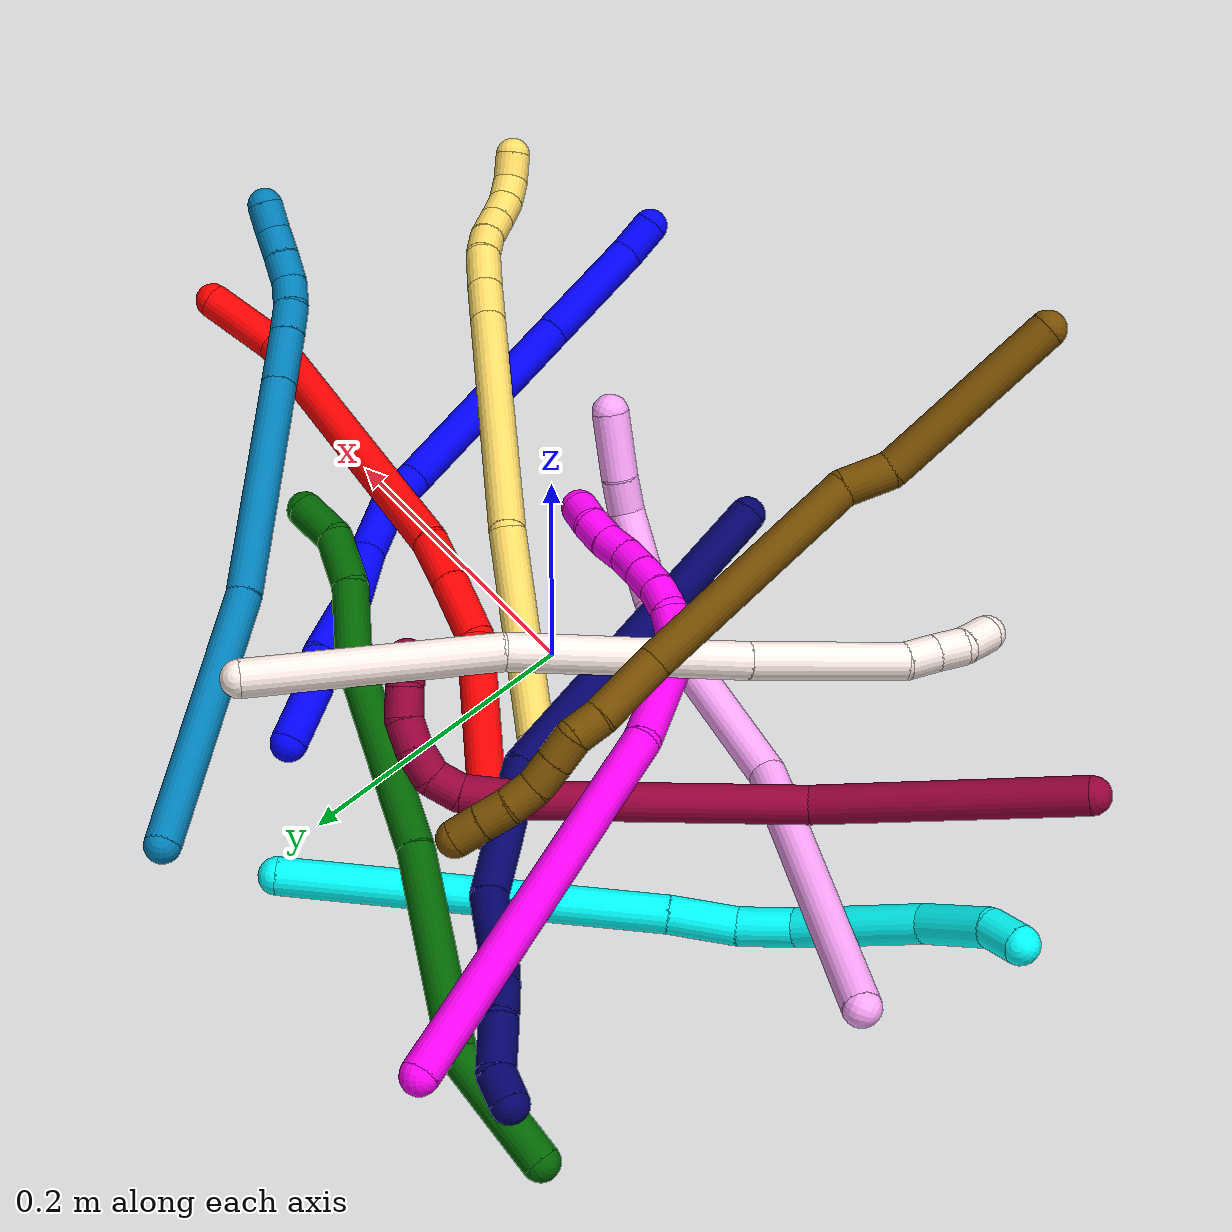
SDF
<sdf version="1.7">
 <world name="default">
  <plugin name="TubeGeneratorPlugin" filename="libtube_generator_plugin.so"/>
  <model name="photoneo_s_sensor">
   <static>1</static>
   <pose>0 0 2 1.57079 1.57079 3.14159</pose>
   <link name="link">
    <inertial><mass>0.1</mass></inertial>
    <sensor name="sensor" type="depth">
     <update_rate>30</update_rate>
     <camera>
      <horizontal_fov>1.22</horizontal_fov>
      <image><width>1920</width><height>1200</height><format>B8G8R8</format></image>
      <clip><near>0.1</near><far>4</far></clip>
      <depth_camera><output>points</output></depth_camera>
     </camera>
     <plugin name="camera_plugin" filename="libgazebo_ros_depth_camera.so">
      <baseline>0.2</baseline>
      <alwaysOn>1</alwaysOn>
      <updateRate>0.0</updateRate>
      <cameraName>camera_ir</cameraName>
      <imageTopicName>/camera/color/image_raw</imageTopicName>
      <cameraInfoTopicName>/camera/color/camera_info</cameraInfoTopicName>
      <depthImageTopicName>/camera/depth/image_raw</depthImageTopicName>
      <depthImageCameraInfoTopicName>/camera/depth/camera_info</depthImageCameraInfoTopicName>
      <pointCloudTopicName>/camera/depth/points</pointCloudTopicName>
      <frameName>fr_optical</frameName>
      <pointCloudCutoff>0.1</pointCloudCutoff>
      <pointCloudCutoffMax>2.0</pointCloudCutoffMax>
      <distortionK1>0</distortionK1>
      <distortionK2>0</distortionK2>
      <distortionK3>0</distortionK3>
      <distortionT1>0</distortionT1>
      <distortionT2>0</distortionT2>
      <CxPrime>0</CxPrime>
      <Cx>0</Cx>
      <Cy>0</Cy>
      <focalLength>0</focalLength>
      <hackBaseline>0</hackBaseline>
     </plugin>
    </sensor>
   </link>
  </model>
  <gravity>0 0 -9.8</gravity>
  <magnetic_field>6e-06 2.3e-05 -4.2e-05</magnetic_field>
  <atmosphere type="adiabatic"/>
  <physics name="default_physics" default="0" type="ode">
   <max_step_size>0.003</max_step_size>
   <real_time_factor>1</real_time_factor>
   <real_time_update_rate>1000</real_time_update_rate>
   <max_contacts>10000</max_contacts>
   <ode>
    <solver>
     <type>quick</type>
     <iters>100</iters>
     <sor>1.3</sor>
     <use_dynamic_moi_rescaling>0</use_dynamic_moi_rescaling>
    </solver>
    <constraints>
     <contact_max_correcting_vel>0</contact_max_correcting_vel>
     <contact_surface_layer>0.001</contact_surface_layer>
     <cfm>0</cfm>
     <erp>0.2</erp>
    </constraints>
   </ode>
  </physics>
  <scene><ambient>0.4 0.4 0.4 1</ambient><background>0.7 0.7 0.7 1</background><shadows>0</shadows></scene>
  <audio><device>default</device></audio>
  <spherical_coordinates>
   <surface_model>EARTH_WGS84</surface_model>
   <latitude_deg>0</latitude_deg>
   <longitude_deg>0</longitude_deg>
   <elevation>0</elevation>
   <heading_deg>0</heading_deg>
  </spherical_coordinates>
  <model name="bin">
   <static>1</static>
   <link name="bottom">
    <collision name="collision-bottom">
     <pose>0 0 -0.01 0 -0 0</pose>
     <geometry><box><size>0.8 0.6 0.02</size></box></geometry>
     <surface>
      <friction><ode><mu>100</mu><mu2>100</mu2></ode></friction>
      <contact><collide_bitmask>65535</collide_bitmask></contact>
     </surface>
    </collision>
   </link>
   <link name="west_wall">
    <collision name="collision-west_wall">
     <pose>-0.41 0 0.1 0 -0 0</pose>
     <geometry><box><size>0.02 0.6 0.2</size></box></geometry>
     <surface>
      <friction><ode><mu>100</mu><mu2>100</mu2></ode></friction>
      <contact><collide_bitmask>65535</collide_bitmask></contact>
     </surface>
    </collision>
   </link>
   <link name="east_wall">
    <collision name="collision-east_wall">
     <pose>0.41 0 0.1 0 -0 0</pose>
     <geometry><box><size>0.02 0.6 0.2</size></box></geometry>
     <surface>
      <friction><ode><mu>100</mu><mu2>100</mu2></ode></friction>
      <contact><collide_bitmask>65535</collide_bitmask></contact>
     </surface>
    </collision>
   </link>
   <link name="south_wall">
    <collision name="collision-south_wall">
     <pose>0 -0.31 0.1 0 -0 0</pose>
     <geometry><box><size>0.8 0.02 0.2</size></box></geometry>
     <surface>
      <friction><ode><mu>100</mu><mu2>100</mu2></ode></friction>
      <contact><collide_bitmask>65535</collide_bitmask></contact>
     </surface>
    </collision>
   </link>
   <link name="north_wall">
    <collision name="collision-north_wall">
     <pose>0 0.31 0.1 0 -0 0</pose>
     <geometry><box><size>0.8 0.02 0.2</size></box></geometry>
     <surface>
      <friction><ode><mu>100</mu><mu2>100</mu2></ode></friction>
      <contact><collide_bitmask>65535</collide_bitmask></contact>
     </surface>
    </collision>
   </link>
  </model>
  <model name="1">
   <static>0</static>
   <link name="1">
    <collision name="collision-cylinder-e_1_1_4">
     <pose>0.000587 0.013724 -0.000368 -1.59761 0.042724 -0.043885</pose>
     <geometry><cylinder><radius>0.0125</radius><length>0.027484</length></cylinder></geometry>
     <surface>
      <friction><ode><mu>1.16</mu><mu2>1.16</mu2><slip1>0</slip1><slip2>0</slip2></ode></friction>
      <contact><ode><kp>1e+06</kp><kd>1</kd><max_vel>0</max_vel><min_depth>0.001</min_depth></ode></contact>
     </surface>
    </collision>
    <visual name="visual-cylinder-e_1_1_4">
     <pose>0.000587 0.013724 -0.000368 -1.59761 0.042724 -0.043885</pose>
     <geometry><cylinder><radius>0.0125</radius><length>0.027484</length></cylinder></geometry>
     <material><ambient>0 0 1 1</ambient></material>
    </visual>
    <collision name="collision-cylinder-e_2_4_5">
     <pose>-0.00126 0.069983 0.005716 -1.42025 -0.056516 0.048593</pose>
     <geometry><cylinder><radius>0.0125</radius><length>0.086179</length></cylinder></geometry>
     <surface>
      <friction><ode><mu>1.16</mu><mu2>1.16</mu2><slip1>0</slip1><slip2>0</slip2></ode></friction>
      <contact><ode><kp>1e+06</kp><kd>1</kd><max_vel>0</max_vel><min_depth>0.001</min_depth></ode></contact>
     </surface>
    </collision>
    <visual name="visual-cylinder-e_2_4_5">
     <pose>-0.00126 0.069983 0.005716 -1.42025 -0.056516 0.048593</pose>
     <geometry><cylinder><radius>0.0125</radius><length>0.086179</length></cylinder></geometry>
     <material><ambient>0 0 1 1</ambient></material>
    </visual>
    <collision name="collision-cylinder-e_3_5_6">
     <pose>-0.008133 0.188635 0.02354 -1.4225 -0.057609 0.049645</pose>
     <geometry><cylinder><radius>0.0125</radius><length>0.154183</length></cylinder></geometry>
     <surface>
      <friction><ode><mu>1.16</mu><mu2>1.16</mu2><slip1>0</slip1><slip2>0</slip2></ode></friction>
      <contact><ode><kp>1e+06</kp><kd>1</kd><max_vel>0</max_vel><min_depth>0.001</min_depth></ode></contact>
     </surface>
    </collision>
    <visual name="visual-cylinder-e_3_5_6">
     <pose>-0.008133 0.188635 0.02354 -1.4225 -0.057609 0.049645</pose>
     <geometry><cylinder><radius>0.0125</radius><length>0.154183</length></cylinder></geometry>
     <material><ambient>0 0 1 1</ambient></material>
    </visual>
    <collision name="collision-cylinder-e_4_6_7">
     <pose>-0.014716 0.27819 0.038653 -1.2992 -0.152539 0.115959</pose>
     <geometry><cylinder><radius>0.0125</radius><length>0.028221</length></cylinder></geometry>
     <surface>
      <friction><ode><mu>1.16</mu><mu2>1.16</mu2><slip1>0</slip1><slip2>0</slip2></ode></friction>
      <contact><ode><kp>1e+06</kp><kd>1</kd><max_vel>0</max_vel><min_depth>0.001</min_depth></ode></contact>
     </surface>
    </collision>
    <visual name="visual-cylinder-e_4_6_7">
     <pose>-0.014716 0.27819 0.038653 -1.2992 -0.152539 0.115959</pose>
     <geometry><cylinder><radius>0.0125</radius><length>0.028221</length></cylinder></geometry>
     <material><ambient>0 0 1 1</ambient></material>
    </visual>
    <collision name="collision-cylinder-e_5_7_8">
     <pose>-0.024779 0.311254 0.043311 -1.52415 -0.383078 0.366011</pose>
     <geometry><cylinder><radius>0.0125</radius><length>0.042372</length></cylinder></geometry>
     <surface>
      <friction><ode><mu>1.16</mu><mu2>1.16</mu2><slip1>0</slip1><slip2>0</slip2></ode></friction>
      <contact><ode><kp>1e+06</kp><kd>1</kd><max_vel>0</max_vel><min_depth>0.001</min_depth></ode></contact>
     </surface>
    </collision>
    <visual name="visual-cylinder-e_5_7_8">
     <pose>-0.024779 0.311254 0.043311 -1.52415 -0.383078 0.366011</pose>
     <geometry><cylinder><radius>0.0125</radius><length>0.042372</length></cylinder></geometry>
     <material><ambient>0 0 1 1</ambient></material>
    </visual>
    <collision name="collision-cylinder-e_6_8_9">
     <pose>-0.043883 0.34843 0.046537 -1.4399 -0.563653 0.497319</pose>
     <geometry><cylinder><radius>0.0125</radius><length>0.041872</length></cylinder></geometry>
     <surface>
      <friction><ode><mu>1.16</mu><mu2>1.16</mu2><slip1>0</slip1><slip2>0</slip2></ode></friction>
      <contact><ode><kp>1e+06</kp><kd>1</kd><max_vel>0</max_vel><min_depth>0.001</min_depth></ode></contact>
     </surface>
    </collision>
    <visual name="visual-cylinder-e_6_8_9">
     <pose>-0.043883 0.34843 0.046537 -1.4399 -0.563653 0.497319</pose>
     <geometry><cylinder><radius>0.0125</radius><length>0.041872</length></cylinder></geometry>
     <material><ambient>0 0 1 1</ambient></material>
    </visual>
    <collision name="collision-cylinder-e_7_9_10">
     <pose>-0.064124 0.388932 0.053757 -1.3601 -0.368154 0.298905</pose>
     <geometry><cylinder><radius>0.0125</radius><length>0.050323</length></cylinder></geometry>
     <surface>
      <friction><ode><mu>1.16</mu><mu2>1.16</mu2><slip1>0</slip1><slip2>0</slip2></ode></friction>
      <contact><ode><kp>1e+06</kp><kd>1</kd><max_vel>0</max_vel><min_depth>0.001</min_depth></ode></contact>
     </surface>
    </collision>
    <visual name="visual-cylinder-e_7_9_10">
     <pose>-0.064124 0.388932 0.053757 -1.3601 -0.368154 0.298905</pose>
     <geometry><cylinder><radius>0.0125</radius><length>0.050323</length></cylinder></geometry>
     <material><ambient>0 0 1 1</ambient></material>
    </visual>
    <collision name="collision-cylinder-e_8_10_11">
     <pose>-0.080553 0.422339 0.058731 -1.56465 -0.614403 0.610865</pose>
     <geometry><cylinder><radius>0.0125</radius><length>0.02558</length></cylinder></geometry>
     <surface>
      <friction><ode><mu>1.16</mu><mu2>1.16</mu2><slip1>0</slip1><slip2>0</slip2></ode></friction>
      <contact><ode><kp>1e+06</kp><kd>1</kd><max_vel>0</max_vel><min_depth>0.001</min_depth></ode></contact>
     </surface>
    </collision>
    <visual name="visual-cylinder-e_8_10_11">
     <pose>-0.080553 0.422339 0.058731 -1.56465 -0.614403 0.610865</pose>
     <geometry><cylinder><radius>0.0125</radius><length>0.02558</length></cylinder></geometry>
     <material><ambient>0 0 1 1</ambient></material>
    </visual>
    <collision name="collision-cylinder-e_9_11_2">
     <pose>-0.095274 0.453407 0.059271 -1.54774 -0.342273 0.334618</pose>
     <geometry><cylinder><radius>0.0125</radius><length>0.043786</length></cylinder></geometry>
     <surface>
      <friction><ode><mu>1.16</mu><mu2>1.16</mu2><slip1>0</slip1><slip2>0</slip2></ode></friction>
      <contact><ode><kp>1e+06</kp><kd>1</kd><max_vel>0</max_vel><min_depth>0.001</min_depth></ode></contact>
     </surface>
    </collision>
    <visual name="visual-cylinder-e_9_11_2">
     <pose>-0.095274 0.453407 0.059271 -1.54774 -0.342273 0.334618</pose>
     <geometry><cylinder><radius>0.0125</radius><length>0.043786</length></cylinder></geometry>
     <material><ambient>0 0 1 1</ambient></material>
    </visual>
    <collision name="collision-sphere-2">
     <pose>-0.102622 0.474025 0.059746 0 -0 0</pose>
     <geometry><sphere><radius>0.0125</radius></sphere></geometry>
     <surface>
      <friction><ode><mu>1.16</mu><mu2>1.16</mu2><slip1>0</slip1><slip2>0</slip2></ode></friction>
      <contact><ode><kp>1e+06</kp><kd>1</kd><max_vel>0</max_vel><min_depth>0.001</min_depth></ode></contact>
     </surface>
    </collision>
    <visual name="visual-sphere-2">
     <pose>-0.102622 0.474025 0.059746 0 -0 0</pose>
     <geometry><sphere><radius>0.0125</radius></sphere></geometry>
     <material><ambient>0 0 1 1</ambient></material>
    </visual>
    <collision name="collision-sphere-11">
     <pose>-0.087926 0.43279 0.058795 0 -0 0</pose>
     <geometry><sphere><radius>0.0125</radius></sphere></geometry>
     <surface>
      <friction><ode><mu>1.16</mu><mu2>1.16</mu2><slip1>0</slip1><slip2>0</slip2></ode></friction>
      <contact><ode><kp>1e+06</kp><kd>1</kd><max_vel>0</max_vel><min_depth>0.001</min_depth></ode></contact>
     </surface>
    </collision>
    <visual name="visual-sphere-11">
     <pose>-0.087926 0.43279 0.058795 0 -0 0</pose>
     <geometry><sphere><radius>0.0125</radius></sphere></geometry>
     <material><ambient>0 0 1 1</ambient></material>
    </visual>
    <collision name="collision-sphere-10">
     <pose>-0.07318 0.411888 0.058667 0 -0 0</pose>
     <geometry><sphere><radius>0.0125</radius></sphere></geometry>
     <surface>
      <friction><ode><mu>1.16</mu><mu2>1.16</mu2><slip1>0</slip1><slip2>0</slip2></ode></friction>
      <contact><ode><kp>1e+06</kp><kd>1</kd><max_vel>0</max_vel><min_depth>0.001</min_depth></ode></contact>
     </surface>
    </collision>
    <visual name="visual-sphere-10">
     <pose>-0.07318 0.411888 0.058667 0 -0 0</pose>
     <geometry><sphere><radius>0.0125</radius></sphere></geometry>
     <material><ambient>0 0 1 1</ambient></material>
    </visual>
    <collision name="collision-sphere-9">
     <pose>-0.055069 0.365975 0.048847 0 -0 0</pose>
     <geometry><sphere><radius>0.0125</radius></sphere></geometry>
     <surface>
      <friction><ode><mu>1.16</mu><mu2>1.16</mu2><slip1>0</slip1><slip2>0</slip2></ode></friction>
      <contact><ode><kp>1e+06</kp><kd>1</kd><max_vel>0</max_vel><min_depth>0.001</min_depth></ode></contact>
     </surface>
    </collision>
    <visual name="visual-sphere-9">
     <pose>-0.055069 0.365975 0.048847 0 -0 0</pose>
     <geometry><sphere><radius>0.0125</radius></sphere></geometry>
     <material><ambient>0 0 1 1</ambient></material>
    </visual>
    <collision name="collision-sphere-4">
     <pose>0.001174 0.027449 -0.000736 0 -0 0</pose>
     <geometry><sphere><radius>0.0125</radius></sphere></geometry>
     <surface>
      <friction><ode><mu>1.16</mu><mu2>1.16</mu2><slip1>0</slip1><slip2>0</slip2></ode></friction>
      <contact><ode><kp>1e+06</kp><kd>1</kd><max_vel>0</max_vel><min_depth>0.001</min_depth></ode></contact>
     </surface>
    </collision>
    <visual name="visual-sphere-4">
     <pose>0.001174 0.027449 -0.000736 0 -0 0</pose>
     <geometry><sphere><radius>0.0125</radius></sphere></geometry>
     <material><ambient>0 0 1 1</ambient></material>
    </visual>
    <collision name="collision-sphere-1">
     <geometry><sphere><radius>0.0125</radius></sphere></geometry>
     <surface>
      <friction><ode><mu>1.16</mu><mu2>1.16</mu2><slip1>0</slip1><slip2>0</slip2></ode></friction>
      <contact><ode><kp>1e+06</kp><kd>1</kd><max_vel>0</max_vel><min_depth>0.001</min_depth></ode></contact>
     </surface>
    </collision>
    <visual name="visual-sphere-1">
     <geometry><sphere><radius>0.0125</radius></sphere></geometry>
     <material><ambient>0 0 1 1</ambient></material>
    </visual>
    <collision name="collision-sphere-8">
     <pose>-0.032697 0.330884 0.044227 0 -0 0</pose>
     <geometry><sphere><radius>0.0125</radius></sphere></geometry>
     <surface>
      <friction><ode><mu>1.16</mu><mu2>1.16</mu2><slip1>0</slip1><slip2>0</slip2></ode></friction>
      <contact><ode><kp>1e+06</kp><kd>1</kd><max_vel>0</max_vel><min_depth>0.001</min_depth></ode></contact>
     </surface>
    </collision>
    <visual name="visual-sphere-8">
     <pose>-0.032697 0.330884 0.044227 0 -0 0</pose>
     <geometry><sphere><radius>0.0125</radius></sphere></geometry>
     <material><ambient>0 0 1 1</ambient></material>
    </visual>
    <collision name="collision-sphere-5">
     <pose>-0.003694 0.112517 0.012168 0 -0 0</pose>
     <geometry><sphere><radius>0.0125</radius></sphere></geometry>
     <surface>
      <friction><ode><mu>1.16</mu><mu2>1.16</mu2><slip1>0</slip1><slip2>0</slip2></ode></friction>
      <contact><ode><kp>1e+06</kp><kd>1</kd><max_vel>0</max_vel><min_depth>0.001</min_depth></ode></contact>
     </surface>
    </collision>
    <visual name="visual-sphere-5">
     <pose>-0.003694 0.112517 0.012168 0 -0 0</pose>
     <geometry><sphere><radius>0.0125</radius></sphere></geometry>
     <material><ambient>0 0 1 1</ambient></material>
    </visual>
    <collision name="collision-sphere-6">
     <pose>-0.012571 0.264754 0.034912 0 -0 0</pose>
     <geometry><sphere><radius>0.0125</radius></sphere></geometry>
     <surface>
      <friction><ode><mu>1.16</mu><mu2>1.16</mu2><slip1>0</slip1><slip2>0</slip2></ode></friction>
      <contact><ode><kp>1e+06</kp><kd>1</kd><max_vel>0</max_vel><min_depth>0.001</min_depth></ode></contact>
     </surface>
    </collision>
    <visual name="visual-sphere-6">
     <pose>-0.012571 0.264754 0.034912 0 -0 0</pose>
     <geometry><sphere><radius>0.0125</radius></sphere></geometry>
     <material><ambient>0 0 1 1</ambient></material>
    </visual>
    <collision name="collision-sphere-7">
     <pose>-0.01686 0.291625 0.042395 0 -0 0</pose>
     <geometry><sphere><radius>0.0125</radius></sphere></geometry>
     <surface>
      <friction><ode><mu>1.16</mu><mu2>1.16</mu2><slip1>0</slip1><slip2>0</slip2></ode></friction>
      <contact><ode><kp>1e+06</kp><kd>1</kd><max_vel>0</max_vel><min_depth>0.001</min_depth></ode></contact>
     </surface>
    </collision>
    <visual name="visual-sphere-7">
     <pose>-0.01686 0.291625 0.042395 0 -0 0</pose>
     <geometry><sphere><radius>0.0125</radius></sphere></geometry>
     <material><ambient>0 0 1 1</ambient></material>
    </visual>
    <inertial>
     <pose>-0.028216 0.2427 0.031579 0 -0 0</pose>
     <mass>0.5</mass>
     <inertia>
      <ixx>0.00043</ixx>
      <ixy>0</ixy>
      <ixz>0</ixz>
      <iyy>0.000135</iyy>
      <iyz>0</iyz>
      <izz>-0.000363</izz>
     </inertia>
    </inertial>
   </link>
   <pose>0.215495 -0.277612 0.033463 -0.235821 0.346695 0.105577</pose>
  </model>
  <model name="2">
   <static>0</static>
   <link name="2">
    <collision name="collision-cylinder-e_1_1_4">
     <pose>0.045548 -0.038793 -0.027961 2.19534 0.761074 1.32667</pose>
     <geometry><cylinder><radius>0.0125</radius><length>0.132081</length></cylinder></geometry>
     <surface>
      <friction><ode><mu>1.16</mu><mu2>1.16</mu2><slip1>0</slip1><slip2>0</slip2></ode></friction>
      <contact><ode><kp>1e+06</kp><kd>1</kd><max_vel>0</max_vel><min_depth>0.001</min_depth></ode></contact>
     </surface>
    </collision>
    <visual name="visual-cylinder-e_1_1_4">
     <pose>0.045548 -0.038793 -0.027961 2.19534 0.761074 1.32667</pose>
     <geometry><cylinder><radius>0.0125</radius><length>0.132081</length></cylinder></geometry>
     <material><ambient>1 0 0 1</ambient></material>
    </visual>
    <collision name="collision-cylinder-e_2_4_5">
     <pose>0.10037 -0.091372 -0.071939 2.43087 0.413554 1.02896</pose>
     <geometry><cylinder><radius>0.0125</radius><length>0.046156</length></cylinder></geometry>
     <surface>
      <friction><ode><mu>1.16</mu><mu2>1.16</mu2><slip1>0</slip1><slip2>0</slip2></ode></friction>
      <contact><ode><kp>1e+06</kp><kd>1</kd><max_vel>0</max_vel><min_depth>0.001</min_depth></ode></contact>
     </surface>
    </collision>
    <visual name="visual-cylinder-e_2_4_5">
     <pose>0.10037 -0.091372 -0.071939 2.43087 0.413554 1.02896</pose>
     <geometry><cylinder><radius>0.0125</radius><length>0.046156</length></cylinder></geometry>
     <material><ambient>1 0 0 1</ambient></material>
    </visual>
    <collision name="collision-cylinder-e_3_5_6">
     <pose>0.116458 -0.115717 -0.100481 2.44124 0.394107 1.00051</pose>
     <geometry><cylinder><radius>0.0125</radius><length>0.035487</length></cylinder></geometry>
     <surface>
      <friction><ode><mu>1.16</mu><mu2>1.16</mu2><slip1>0</slip1><slip2>0</slip2></ode></friction>
      <contact><ode><kp>1e+06</kp><kd>1</kd><max_vel>0</max_vel><min_depth>0.001</min_depth></ode></contact>
     </surface>
    </collision>
    <visual name="visual-cylinder-e_3_5_6">
     <pose>0.116458 -0.115717 -0.100481 2.44124 0.394107 1.00051</pose>
     <geometry><cylinder><radius>0.0125</radius><length>0.035487</length></cylinder></geometry>
     <material><ambient>1 0 0 1</ambient></material>
    </visual>
    <collision name="collision-cylinder-e_4_6_7">
     <pose>0.144912 -0.194094 -0.203033 2.49596 0.189698 0.554159</pose>
     <geometry><cylinder><radius>0.0125</radius><length>0.22954</length></cylinder></geometry>
     <surface>
      <friction><ode><mu>1.16</mu><mu2>1.16</mu2><slip1>0</slip1><slip2>0</slip2></ode></friction>
      <contact><ode><kp>1e+06</kp><kd>1</kd><max_vel>0</max_vel><min_depth>0.001</min_depth></ode></contact>
     </surface>
    </collision>
    <visual name="visual-cylinder-e_4_6_7">
     <pose>0.144912 -0.194094 -0.203033 2.49596 0.189698 0.554159</pose>
     <geometry><cylinder><radius>0.0125</radius><length>0.22954</length></cylinder></geometry>
     <material><ambient>1 0 0 1</ambient></material>
    </visual>
    <collision name="collision-cylinder-e_5_7_2">
     <pose>0.173831 -0.266074 -0.320159 2.98923 0.259439 2.08281</pose>
     <geometry><cylinder><radius>0.0125</radius><length>0.056737</length></cylinder></geometry>
     <surface>
      <friction><ode><mu>1.16</mu><mu2>1.16</mu2><slip1>0</slip1><slip2>0</slip2></ode></friction>
      <contact><ode><kp>1e+06</kp><kd>1</kd><max_vel>0</max_vel><min_depth>0.001</min_depth></ode></contact>
     </surface>
    </collision>
    <visual name="visual-cylinder-e_5_7_2">
     <pose>0.173831 -0.266074 -0.320159 2.98923 0.259439 2.08281</pose>
     <geometry><cylinder><radius>0.0125</radius><length>0.056737</length></cylinder></geometry>
     <material><ambient>1 0 0 1</ambient></material>
    </visual>
    <collision name="collision-sphere-2">
     <pose>0.181109 -0.270235 -0.347261 0 -0 0</pose>
     <geometry><sphere><radius>0.0125</radius></sphere></geometry>
     <surface>
      <friction><ode><mu>1.16</mu><mu2>1.16</mu2><slip1>0</slip1><slip2>0</slip2></ode></friction>
      <contact><ode><kp>1e+06</kp><kd>1</kd><max_vel>0</max_vel><min_depth>0.001</min_depth></ode></contact>
     </surface>
    </collision>
    <visual name="visual-sphere-2">
     <pose>0.181109 -0.270235 -0.347261 0 -0 0</pose>
     <geometry><sphere><radius>0.0125</radius></sphere></geometry>
     <material><ambient>1 0 0 1</ambient></material>
    </visual>
    <collision name="collision-sphere-7">
     <pose>0.166553 -0.261913 -0.293058 0 -0 0</pose>
     <geometry><sphere><radius>0.0125</radius></sphere></geometry>
     <surface>
      <friction><ode><mu>1.16</mu><mu2>1.16</mu2><slip1>0</slip1><slip2>0</slip2></ode></friction>
      <contact><ode><kp>1e+06</kp><kd>1</kd><max_vel>0</max_vel><min_depth>0.001</min_depth></ode></contact>
     </surface>
    </collision>
    <visual name="visual-sphere-7">
     <pose>0.166553 -0.261913 -0.293058 0 -0 0</pose>
     <geometry><sphere><radius>0.0125</radius></sphere></geometry>
     <material><ambient>1 0 0 1</ambient></material>
    </visual>
    <collision name="collision-sphere-6">
     <pose>0.123271 -0.126276 -0.113008 0 -0 0</pose>
     <geometry><sphere><radius>0.0125</radius></sphere></geometry>
     <surface>
      <friction><ode><mu>1.16</mu><mu2>1.16</mu2><slip1>0</slip1><slip2>0</slip2></ode></friction>
      <contact><ode><kp>1e+06</kp><kd>1</kd><max_vel>0</max_vel><min_depth>0.001</min_depth></ode></contact>
     </surface>
    </collision>
    <visual name="visual-sphere-6">
     <pose>0.123271 -0.126276 -0.113008 0 -0 0</pose>
     <geometry><sphere><radius>0.0125</radius></sphere></geometry>
     <material><ambient>1 0 0 1</ambient></material>
    </visual>
    <collision name="collision-sphere-5">
     <pose>0.109644 -0.105158 -0.087954 0 -0 0</pose>
     <geometry><sphere><radius>0.0125</radius></sphere></geometry>
     <surface>
      <friction><ode><mu>1.16</mu><mu2>1.16</mu2><slip1>0</slip1><slip2>0</slip2></ode></friction>
      <contact><ode><kp>1e+06</kp><kd>1</kd><max_vel>0</max_vel><min_depth>0.001</min_depth></ode></contact>
     </surface>
    </collision>
    <visual name="visual-sphere-5">
     <pose>0.109644 -0.105158 -0.087954 0 -0 0</pose>
     <geometry><sphere><radius>0.0125</radius></sphere></geometry>
     <material><ambient>1 0 0 1</ambient></material>
    </visual>
    <collision name="collision-sphere-1">
     <geometry><sphere><radius>0.0125</radius></sphere></geometry>
     <surface>
      <friction><ode><mu>1.16</mu><mu2>1.16</mu2><slip1>0</slip1><slip2>0</slip2></ode></friction>
      <contact><ode><kp>1e+06</kp><kd>1</kd><max_vel>0</max_vel><min_depth>0.001</min_depth></ode></contact>
     </surface>
    </collision>
    <visual name="visual-sphere-1">
     <geometry><sphere><radius>0.0125</radius></sphere></geometry>
     <material><ambient>1 0 0 1</ambient></material>
    </visual>
    <collision name="collision-sphere-4">
     <pose>0.091096 -0.077585 -0.055923 0 -0 0</pose>
     <geometry><sphere><radius>0.0125</radius></sphere></geometry>
     <surface>
      <friction><ode><mu>1.16</mu><mu2>1.16</mu2><slip1>0</slip1><slip2>0</slip2></ode></friction>
      <contact><ode><kp>1e+06</kp><kd>1</kd><max_vel>0</max_vel><min_depth>0.001</min_depth></ode></contact>
     </surface>
    </collision>
    <visual name="visual-sphere-4">
     <pose>0.091096 -0.077585 -0.055923 0 -0 0</pose>
     <geometry><sphere><radius>0.0125</radius></sphere></geometry>
     <material><ambient>1 0 0 1</ambient></material>
    </visual>
    <inertial>
     <pose>0.115814 -0.146192 -0.150697 0 -0 0</pose>
     <mass>0.5</mass>
     <inertia>
      <ixx>0.001587</ixx>
      <ixy>0</ixy>
      <ixz>0</ixz>
      <iyy>0.000125</iyy>
      <iyz>0</iyz>
      <izz>0.000363</izz>
     </inertia>
    </inertial>
   </link>
   <pose>-0.082043 0.123573 0.012476 1.5682 -1.00254 -1.08204</pose>
  </model>
  <model name="3">
   <static>0</static>
   <link name="3">
    <collision name="collision-cylinder-e_1_1_4">
     <pose>-0.068762 -0.102121 0.024485 1.33547 -0.579728 -0.46201</pose>
     <geometry><cylinder><radius>0.0125</radius><length>0.25105</length></cylinder></geometry>
     <surface>
      <friction><ode><mu>1.16</mu><mu2>1.16</mu2><slip1>0</slip1><slip2>0</slip2></ode></friction>
      <contact><ode><kp>1e+06</kp><kd>1</kd><max_vel>0</max_vel><min_depth>0.001</min_depth></ode></contact>
     </surface>
    </collision>
    <visual name="visual-cylinder-e_1_1_4">
     <pose>-0.068762 -0.102121 0.024485 1.33547 -0.579728 -0.46201</pose>
     <geometry><cylinder><radius>0.0125</radius><length>0.25105</length></cylinder></geometry>
     <material><ambient>0.003922 1 0.996078 1</ambient></material>
    </visual>
    <collision name="collision-cylinder-e_2_4_5">
     <pose>-0.14841 -0.223169 0.05291 1.36558 -0.512849 -0.420189</pose>
     <geometry><cylinder><radius>0.0125</radius><length>0.044373</length></cylinder></geometry>
     <surface>
      <friction><ode><mu>1.16</mu><mu2>1.16</mu2><slip1>0</slip1><slip2>0</slip2></ode></friction>
      <contact><ode><kp>1e+06</kp><kd>1</kd><max_vel>0</max_vel><min_depth>0.001</min_depth></ode></contact>
     </surface>
    </collision>
    <visual name="visual-cylinder-e_2_4_5">
     <pose>-0.14841 -0.223169 0.05291 1.36558 -0.512849 -0.420189</pose>
     <geometry><cylinder><radius>0.0125</radius><length>0.044373</length></cylinder></geometry>
     <material><ambient>0.003922 1 0.996078 1</ambient></material>
    </visual>
    <collision name="collision-cylinder-e_3_5_6">
     <pose>-0.171051 -0.256607 0.05695 1.5639 -0.680803 -0.676476</pose>
     <geometry><cylinder><radius>0.0125</radius><length>0.03735</length></cylinder></geometry>
     <surface>
      <friction><ode><mu>1.16</mu><mu2>1.16</mu2><slip1>0</slip1><slip2>0</slip2></ode></friction>
      <contact><ode><kp>1e+06</kp><kd>1</kd><max_vel>0</max_vel><min_depth>0.001</min_depth></ode></contact>
     </surface>
    </collision>
    <visual name="visual-cylinder-e_3_5_6">
     <pose>-0.171051 -0.256607 0.05695 1.5639 -0.680803 -0.676476</pose>
     <geometry><cylinder><radius>0.0125</radius><length>0.03735</length></cylinder></geometry>
     <material><ambient>0.003922 1 0.996078 1</ambient></material>
    </visual>
    <collision name="collision-cylinder-e_4_6_7">
     <pose>-0.211888 -0.302415 0.042945 1.9942 -0.702872 -1.03222</pose>
     <geometry><cylinder><radius>0.0125</radius><length>0.089985</length></cylinder></geometry>
     <surface>
      <friction><ode><mu>1.16</mu><mu2>1.16</mu2><slip1>0</slip1><slip2>0</slip2></ode></friction>
      <contact><ode><kp>1e+06</kp><kd>1</kd><max_vel>0</max_vel><min_depth>0.001</min_depth></ode></contact>
     </surface>
    </collision>
    <visual name="visual-cylinder-e_4_6_7">
     <pose>-0.211888 -0.302415 0.042945 1.9942 -0.702872 -1.03222</pose>
     <geometry><cylinder><radius>0.0125</radius><length>0.089985</length></cylinder></geometry>
     <material><ambient>0.003922 1 0.996078 1</ambient></material>
    </visual>
    <collision name="collision-cylinder-e_5_7_8">
     <pose>-0.25458 -0.350454 0.014808 2.26841 -0.557115 -1.0997</pose>
     <geometry><cylinder><radius>0.0125</radius><length>0.051473</length></cylinder></geometry>
     <surface>
      <friction><ode><mu>1.16</mu><mu2>1.16</mu2><slip1>0</slip1><slip2>0</slip2></ode></friction>
      <contact><ode><kp>1e+06</kp><kd>1</kd><max_vel>0</max_vel><min_depth>0.001</min_depth></ode></contact>
     </surface>
    </collision>
    <visual name="visual-cylinder-e_5_7_8">
     <pose>-0.25458 -0.350454 0.014808 2.26841 -0.557115 -1.0997</pose>
     <geometry><cylinder><radius>0.0125</radius><length>0.051473</length></cylinder></geometry>
     <material><ambient>0.003922 1 0.996078 1</ambient></material>
    </visual>
    <collision name="collision-cylinder-e_6_8_2">
     <pose>-0.270812 -0.377533 -0.006455 2.1811 -0.20512 -0.390123</pose>
     <geometry><cylinder><radius>0.0125</radius><length>0.02577</length></cylinder></geometry>
     <surface>
      <friction><ode><mu>1.16</mu><mu2>1.16</mu2><slip1>0</slip1><slip2>0</slip2></ode></friction>
      <contact><ode><kp>1e+06</kp><kd>1</kd><max_vel>0</max_vel><min_depth>0.001</min_depth></ode></contact>
     </surface>
    </collision>
    <visual name="visual-cylinder-e_6_8_2">
     <pose>-0.270812 -0.377533 -0.006455 2.1811 -0.20512 -0.390123</pose>
     <geometry><cylinder><radius>0.0125</radius><length>0.02577</length></cylinder></geometry>
     <material><ambient>0.003922 1 0.996078 1</ambient></material>
    </visual>
    <collision name="collision-sphere-2">
     <pose>-0.273437 -0.38787 -0.013684 0 -0 0</pose>
     <geometry><sphere><radius>0.0125</radius></sphere></geometry>
     <surface>
      <friction><ode><mu>1.16</mu><mu2>1.16</mu2><slip1>0</slip1><slip2>0</slip2></ode></friction>
      <contact><ode><kp>1e+06</kp><kd>1</kd><max_vel>0</max_vel><min_depth>0.001</min_depth></ode></contact>
     </surface>
    </collision>
    <visual name="visual-sphere-2">
     <pose>-0.273437 -0.38787 -0.013684 0 -0 0</pose>
     <geometry><sphere><radius>0.0125</radius></sphere></geometry>
     <material><ambient>0.003922 1 0.996078 1</ambient></material>
    </visual>
    <collision name="collision-sphere-4">
     <pose>-0.137524 -0.204242 0.048971 0 -0 0</pose>
     <geometry><sphere><radius>0.0125</radius></sphere></geometry>
     <surface>
      <friction><ode><mu>1.16</mu><mu2>1.16</mu2><slip1>0</slip1><slip2>0</slip2></ode></friction>
      <contact><ode><kp>1e+06</kp><kd>1</kd><max_vel>0</max_vel><min_depth>0.001</min_depth></ode></contact>
     </surface>
    </collision>
    <visual name="visual-sphere-4">
     <pose>-0.137524 -0.204242 0.048971 0 -0 0</pose>
     <geometry><sphere><radius>0.0125</radius></sphere></geometry>
     <material><ambient>0.003922 1 0.996078 1</ambient></material>
    </visual>
    <collision name="collision-sphere-1">
     <geometry><sphere><radius>0.0125</radius></sphere></geometry>
     <surface>
      <friction><ode><mu>1.16</mu><mu2>1.16</mu2><slip1>0</slip1><slip2>0</slip2></ode></friction>
      <contact><ode><kp>1e+06</kp><kd>1</kd><max_vel>0</max_vel><min_depth>0.001</min_depth></ode></contact>
     </surface>
    </collision>
    <visual name="visual-sphere-1">
     <geometry><sphere><radius>0.0125</radius></sphere></geometry>
     <material><ambient>0.003922 1 0.996078 1</ambient></material>
    </visual>
    <collision name="collision-sphere-8">
     <pose>-0.268188 -0.367195 0.000775 0 -0 0</pose>
     <geometry><sphere><radius>0.0125</radius></sphere></geometry>
     <surface>
      <friction><ode><mu>1.16</mu><mu2>1.16</mu2><slip1>0</slip1><slip2>0</slip2></ode></friction>
      <contact><ode><kp>1e+06</kp><kd>1</kd><max_vel>0</max_vel><min_depth>0.001</min_depth></ode></contact>
     </surface>
    </collision>
    <visual name="visual-sphere-8">
     <pose>-0.268188 -0.367195 0.000775 0 -0 0</pose>
     <geometry><sphere><radius>0.0125</radius></sphere></geometry>
     <material><ambient>0.003922 1 0.996078 1</ambient></material>
    </visual>
    <collision name="collision-sphere-5">
     <pose>-0.159296 -0.242096 0.05685 0 -0 0</pose>
     <geometry><sphere><radius>0.0125</radius></sphere></geometry>
     <surface>
      <friction><ode><mu>1.16</mu><mu2>1.16</mu2><slip1>0</slip1><slip2>0</slip2></ode></friction>
      <contact><ode><kp>1e+06</kp><kd>1</kd><max_vel>0</max_vel><min_depth>0.001</min_depth></ode></contact>
     </surface>
    </collision>
    <visual name="visual-sphere-5">
     <pose>-0.159296 -0.242096 0.05685 0 -0 0</pose>
     <geometry><sphere><radius>0.0125</radius></sphere></geometry>
     <material><ambient>0.003922 1 0.996078 1</ambient></material>
    </visual>
    <collision name="collision-sphere-6">
     <pose>-0.182805 -0.271118 0.05705 0 -0 0</pose>
     <geometry><sphere><radius>0.0125</radius></sphere></geometry>
     <surface>
      <friction><ode><mu>1.16</mu><mu2>1.16</mu2><slip1>0</slip1><slip2>0</slip2></ode></friction>
      <contact><ode><kp>1e+06</kp><kd>1</kd><max_vel>0</max_vel><min_depth>0.001</min_depth></ode></contact>
     </surface>
    </collision>
    <visual name="visual-sphere-6">
     <pose>-0.182805 -0.271118 0.05705 0 -0 0</pose>
     <geometry><sphere><radius>0.0125</radius></sphere></geometry>
     <material><ambient>0.003922 1 0.996078 1</ambient></material>
    </visual>
    <collision name="collision-sphere-7">
     <pose>-0.240972 -0.333713 0.028841 0 -0 0</pose>
     <geometry><sphere><radius>0.0125</radius></sphere></geometry>
     <surface>
      <friction><ode><mu>1.16</mu><mu2>1.16</mu2><slip1>0</slip1><slip2>0</slip2></ode></friction>
      <contact><ode><kp>1e+06</kp><kd>1</kd><max_vel>0</max_vel><min_depth>0.001</min_depth></ode></contact>
     </surface>
    </collision>
    <visual name="visual-sphere-7">
     <pose>-0.240972 -0.333713 0.028841 0 -0 0</pose>
     <geometry><sphere><radius>0.0125</radius></sphere></geometry>
     <material><ambient>0.003922 1 0.996078 1</ambient></material>
    </visual>
    <inertial>
     <pose>-0.138773 -0.20021 0.030164 0 -0 0</pose>
     <mass>0.5</mass>
     <inertia>
      <ixx>0.000462</ixx>
      <ixy>0</ixy>
      <ixz>0</ixz>
      <iyy>3.2e-05</iyy>
      <iyz>0</iyz>
      <izz>0.001932</izz>
     </inertia>
    </inertial>
   </link>
   <pose>-0.016723 0.245797 0.010914 2.97542 0.551251 1.62671</pose>
  </model>
  <model name="4">
   <static>0</static>
   <link name="4">
    <collision name="collision-cylinder-e_1_1_4">
     <pose>0.06943 -0.047461 -0.066941 2.52486 0.702227 1.71006</pose>
     <geometry><cylinder><radius>0.0125</radius><length>0.214981</length></cylinder></geometry>
     <surface>
      <friction><ode><mu>1.16</mu><mu2>1.16</mu2><slip1>0</slip1><slip2>0</slip2></ode></friction>
      <contact><ode><kp>1e+06</kp><kd>1</kd><max_vel>0</max_vel><min_depth>0.001</min_depth></ode></contact>
     </surface>
    </collision>
    <visual name="visual-cylinder-e_1_1_4">
     <pose>0.06943 -0.047461 -0.066941 2.52486 0.702227 1.71006</pose>
     <geometry><cylinder><radius>0.0125</radius><length>0.214981</length></cylinder></geometry>
     <material><ambient>1 0.65098 0.996078 1</ambient></material>
    </visual>
    <collision name="collision-cylinder-e_2_4_5">
     <pose>0.164417 -0.101709 -0.176482 2.98358 0.534853 2.579</pose>
     <geometry><cylinder><radius>0.0125</radius><length>0.100276</length></cylinder></geometry>
     <surface>
      <friction><ode><mu>1.16</mu><mu2>1.16</mu2><slip1>0</slip1><slip2>0</slip2></ode></friction>
      <contact><ode><kp>1e+06</kp><kd>1</kd><max_vel>0</max_vel><min_depth>0.001</min_depth></ode></contact>
     </surface>
    </collision>
    <visual name="visual-cylinder-e_2_4_5">
     <pose>0.164417 -0.101709 -0.176482 2.98358 0.534853 2.579</pose>
     <geometry><cylinder><radius>0.0125</radius><length>0.100276</length></cylinder></geometry>
     <material><ambient>1 0.65098 0.996078 1</ambient></material>
    </visual>
    <collision name="collision-cylinder-e_3_5_6">
     <pose>0.205377 -0.108451 -0.240307 -3.13945 0.627764 -3.13498</pose>
     <geometry><cylinder><radius>0.0125</radius><length>0.052455</length></cylinder></geometry>
     <surface>
      <friction><ode><mu>1.16</mu><mu2>1.16</mu2><slip1>0</slip1><slip2>0</slip2></ode></friction>
      <contact><ode><kp>1e+06</kp><kd>1</kd><max_vel>0</max_vel><min_depth>0.001</min_depth></ode></contact>
     </surface>
    </collision>
    <visual name="visual-cylinder-e_3_5_6">
     <pose>0.205377 -0.108451 -0.240307 -3.13945 0.627764 -3.13498</pose>
     <geometry><cylinder><radius>0.0125</radius><length>0.052455</length></cylinder></geometry>
     <material><ambient>1 0.65098 0.996078 1</ambient></material>
    </visual>
    <collision name="collision-cylinder-e_4_6_7">
     <pose>0.242166 -0.097955 -0.281722 -2.6639 0.754846 -2.03996</pose>
     <geometry><cylinder><radius>0.0125</radius><length>0.06242</length></cylinder></geometry>
     <surface>
      <friction><ode><mu>1.16</mu><mu2>1.16</mu2><slip1>0</slip1><slip2>0</slip2></ode></friction>
      <contact><ode><kp>1e+06</kp><kd>1</kd><max_vel>0</max_vel><min_depth>0.001</min_depth></ode></contact>
     </surface>
    </collision>
    <visual name="visual-cylinder-e_4_6_7">
     <pose>0.242166 -0.097955 -0.281722 -2.6639 0.754846 -2.03996</pose>
     <geometry><cylinder><radius>0.0125</radius><length>0.06242</length></cylinder></geometry>
     <material><ambient>1 0.65098 0.996078 1</ambient></material>
    </visual>
    <collision name="collision-cylinder-e_5_7_8">
     <pose>0.27037 -0.078663 -0.30734 -2.12161 0.581462 -0.982394</pose>
     <geometry><cylinder><radius>0.0125</radius><length>0.024832</length></cylinder></geometry>
     <surface>
      <friction><ode><mu>1.16</mu><mu2>1.16</mu2><slip1>0</slip1><slip2>0</slip2></ode></friction>
      <contact><ode><kp>1e+06</kp><kd>1</kd><max_vel>0</max_vel><min_depth>0.001</min_depth></ode></contact>
     </surface>
    </collision>
    <visual name="visual-cylinder-e_5_7_8">
     <pose>0.27037 -0.078663 -0.30734 -2.12161 0.581462 -0.982394</pose>
     <geometry><cylinder><radius>0.0125</radius><length>0.024832</length></cylinder></geometry>
     <material><ambient>1 0.65098 0.996078 1</ambient></material>
    </visual>
    <collision name="collision-cylinder-e_6_8_2">
     <pose>0.291604 -0.055678 -0.322732 -2.18439 0.694688 -1.21845</pose>
     <geometry><cylinder><radius>0.0125</radius><length>0.045036</length></cylinder></geometry>
     <surface>
      <friction><ode><mu>1.16</mu><mu2>1.16</mu2><slip1>0</slip1><slip2>0</slip2></ode></friction>
      <contact><ode><kp>1e+06</kp><kd>1</kd><max_vel>0</max_vel><min_depth>0.001</min_depth></ode></contact>
     </surface>
    </collision>
    <visual name="visual-cylinder-e_6_8_2">
     <pose>0.291604 -0.055678 -0.322732 -2.18439 0.694688 -1.21845</pose>
     <geometry><cylinder><radius>0.0125</radius><length>0.045036</length></cylinder></geometry>
     <material><ambient>1 0.65098 0.996078 1</ambient></material>
    </visual>
    <collision name="collision-sphere-2">
     <pose>0.306018 -0.041534 -0.332693 0 -0 0</pose>
     <geometry><sphere><radius>0.0125</radius></sphere></geometry>
     <surface>
      <friction><ode><mu>1.16</mu><mu2>1.16</mu2><slip1>0</slip1><slip2>0</slip2></ode></friction>
      <contact><ode><kp>1e+06</kp><kd>1</kd><max_vel>0</max_vel><min_depth>0.001</min_depth></ode></contact>
     </surface>
    </collision>
    <visual name="visual-sphere-2">
     <pose>0.306018 -0.041534 -0.332693 0 -0 0</pose>
     <geometry><sphere><radius>0.0125</radius></sphere></geometry>
     <material><ambient>1 0.65098 0.996078 1</ambient></material>
    </visual>
    <collision name="collision-sphere-4">
     <pose>0.138861 -0.094921 -0.133883 0 -0 0</pose>
     <geometry><sphere><radius>0.0125</radius></sphere></geometry>
     <surface>
      <friction><ode><mu>1.16</mu><mu2>1.16</mu2><slip1>0</slip1><slip2>0</slip2></ode></friction>
      <contact><ode><kp>1e+06</kp><kd>1</kd><max_vel>0</max_vel><min_depth>0.001</min_depth></ode></contact>
     </surface>
    </collision>
    <visual name="visual-sphere-4">
     <pose>0.138861 -0.094921 -0.133883 0 -0 0</pose>
     <geometry><sphere><radius>0.0125</radius></sphere></geometry>
     <material><ambient>1 0.65098 0.996078 1</ambient></material>
    </visual>
    <collision name="collision-sphere-1">
     <geometry><sphere><radius>0.0125</radius></sphere></geometry>
     <surface>
      <friction><ode><mu>1.16</mu><mu2>1.16</mu2><slip1>0</slip1><slip2>0</slip2></ode></friction>
      <contact><ode><kp>1e+06</kp><kd>1</kd><max_vel>0</max_vel><min_depth>0.001</min_depth></ode></contact>
     </surface>
    </collision>
    <visual name="visual-sphere-1">
     <geometry><sphere><radius>0.0125</radius></sphere></geometry>
     <material><ambient>1 0.65098 0.996078 1</ambient></material>
    </visual>
    <collision name="collision-sphere-8">
     <pose>0.277189 -0.069822 -0.31277 0 -0 0</pose>
     <geometry><sphere><radius>0.0125</radius></sphere></geometry>
     <surface>
      <friction><ode><mu>1.16</mu><mu2>1.16</mu2><slip1>0</slip1><slip2>0</slip2></ode></friction>
      <contact><ode><kp>1e+06</kp><kd>1</kd><max_vel>0</max_vel><min_depth>0.001</min_depth></ode></contact>
     </surface>
    </collision>
    <visual name="visual-sphere-8">
     <pose>0.277189 -0.069822 -0.31277 0 -0 0</pose>
     <geometry><sphere><radius>0.0125</radius></sphere></geometry>
     <material><ambient>1 0.65098 0.996078 1</ambient></material>
    </visual>
    <collision name="collision-sphere-5">
     <pose>0.189973 -0.108497 -0.21908 0 -0 0</pose>
     <geometry><sphere><radius>0.0125</radius></sphere></geometry>
     <surface>
      <friction><ode><mu>1.16</mu><mu2>1.16</mu2><slip1>0</slip1><slip2>0</slip2></ode></friction>
      <contact><ode><kp>1e+06</kp><kd>1</kd><max_vel>0</max_vel><min_depth>0.001</min_depth></ode></contact>
     </surface>
    </collision>
    <visual name="visual-sphere-5">
     <pose>0.189973 -0.108497 -0.21908 0 -0 0</pose>
     <geometry><sphere><radius>0.0125</radius></sphere></geometry>
     <material><ambient>1 0.65098 0.996078 1</ambient></material>
    </visual>
    <collision name="collision-sphere-6">
     <pose>0.220781 -0.108406 -0.261534 0 -0 0</pose>
     <geometry><sphere><radius>0.0125</radius></sphere></geometry>
     <surface>
      <friction><ode><mu>1.16</mu><mu2>1.16</mu2><slip1>0</slip1><slip2>0</slip2></ode></friction>
      <contact><ode><kp>1e+06</kp><kd>1</kd><max_vel>0</max_vel><min_depth>0.001</min_depth></ode></contact>
     </surface>
    </collision>
    <visual name="visual-sphere-6">
     <pose>0.220781 -0.108406 -0.261534 0 -0 0</pose>
     <geometry><sphere><radius>0.0125</radius></sphere></geometry>
     <material><ambient>1 0.65098 0.996078 1</ambient></material>
    </visual>
    <collision name="collision-sphere-7">
     <pose>0.26355 -0.087504 -0.30191 0 -0 0</pose>
     <geometry><sphere><radius>0.0125</radius></sphere></geometry>
     <surface>
      <friction><ode><mu>1.16</mu><mu2>1.16</mu2><slip1>0</slip1><slip2>0</slip2></ode></friction>
      <contact><ode><kp>1e+06</kp><kd>1</kd><max_vel>0</max_vel><min_depth>0.001</min_depth></ode></contact>
     </surface>
    </collision>
    <visual name="visual-sphere-7">
     <pose>0.26355 -0.087504 -0.30191 0 -0 0</pose>
     <geometry><sphere><radius>0.0125</radius></sphere></geometry>
     <material><ambient>1 0.65098 0.996078 1</ambient></material>
    </visual>
    <inertial>
     <pose>0.154297 -0.073332 -0.168889 0 -0 0</pose>
     <mass>0.5</mass>
     <inertia>
      <ixx>0.000505</ixx>
      <ixy>0</ixy>
      <ixz>0</ixz>
      <iyy>0.00116</iyy>
      <iyz>0</iyz>
      <izz>-0.000276</izz>
     </inertia>
    </inertial>
   </link>
   <pose>-0.347768 0.055142 0.086393 1.56895 -0.174569 -1.20448</pose>
  </model>
  <model name="5">
   <static>0</static>
   <link name="5">
    <collision name="collision-cylinder-e_1_1_4">
     <pose>0.007919 0.009028 0.070058 -0.12816 0.111646 -0.007171</pose>
     <geometry><cylinder><radius>0.0125</radius><length>0.142159</length></cylinder></geometry>
     <surface>
      <friction><ode><mu>1.16</mu><mu2>1.16</mu2><slip1>0</slip1><slip2>0</slip2></ode></friction>
      <contact><ode><kp>1e+06</kp><kd>1</kd><max_vel>0</max_vel><min_depth>0.001</min_depth></ode></contact>
     </surface>
    </collision>
    <visual name="visual-cylinder-e_1_1_4">
     <pose>0.007919 0.009028 0.070058 -0.12816 0.111646 -0.007171</pose>
     <geometry><cylinder><radius>0.0125</radius><length>0.142159</length></cylinder></geometry>
     <material><ambient>1 0.858824 0.4 1</ambient></material>
    </visual>
    <collision name="collision-cylinder-e_2_4_5">
     <pose>0.043481 -0.002175 0.229282 0.223115 0.293588 0.033124</pose>
     <geometry><cylinder><radius>0.0125</radius><length>0.191041</length></cylinder></geometry>
     <surface>
      <friction><ode><mu>1.16</mu><mu2>1.16</mu2><slip1>0</slip1><slip2>0</slip2></ode></friction>
      <contact><ode><kp>1e+06</kp><kd>1</kd><max_vel>0</max_vel><min_depth>0.001</min_depth></ode></contact>
     </surface>
    </collision>
    <visual name="visual-cylinder-e_2_4_5">
     <pose>0.043481 -0.002175 0.229282 0.223115 0.293588 0.033124</pose>
     <geometry><cylinder><radius>0.0125</radius><length>0.191041</length></cylinder></geometry>
     <material><ambient>1 0.858824 0.4 1</ambient></material>
    </visual>
    <collision name="collision-cylinder-e_3_5_6">
     <pose>0.075811 -0.02588 0.333593 0.225465 0.293002 0.033408</pose>
     <geometry><cylinder><radius>0.0125</radius><length>0.032457</length></cylinder></geometry>
     <surface>
      <friction><ode><mu>1.16</mu><mu2>1.16</mu2><slip1>0</slip1><slip2>0</slip2></ode></friction>
      <contact><ode><kp>1e+06</kp><kd>1</kd><max_vel>0</max_vel><min_depth>0.001</min_depth></ode></contact>
     </surface>
    </collision>
    <visual name="visual-cylinder-e_3_5_6">
     <pose>0.075811 -0.02588 0.333593 0.225465 0.293002 0.033408</pose>
     <geometry><cylinder><radius>0.0125</radius><length>0.032457</length></cylinder></geometry>
     <material><ambient>1 0.858824 0.4 1</ambient></material>
    </visual>
    <collision name="collision-cylinder-e_4_6_7">
     <pose>0.084431 -0.032376 0.363849 0.19739 0.249852 0.024868</pose>
     <geometry><cylinder><radius>0.0125</radius><length>0.031812</length></cylinder></geometry>
     <surface>
      <friction><ode><mu>1.16</mu><mu2>1.16</mu2><slip1>0</slip1><slip2>0</slip2></ode></friction>
      <contact><ode><kp>1e+06</kp><kd>1</kd><max_vel>0</max_vel><min_depth>0.001</min_depth></ode></contact>
     </surface>
    </collision>
    <visual name="visual-cylinder-e_4_6_7">
     <pose>0.084431 -0.032376 0.363849 0.19739 0.249852 0.024868</pose>
     <geometry><cylinder><radius>0.0125</radius><length>0.031812</length></cylinder></geometry>
     <material><ambient>1 0.858824 0.4 1</ambient></material>
    </visual>
    <collision name="collision-cylinder-e_5_7_8">
     <pose>0.090032 -0.039379 0.388057 0.412586 0.166474 0.034915</pose>
     <geometry><cylinder><radius>0.0125</radius><length>0.020135</length></cylinder></geometry>
     <surface>
      <friction><ode><mu>1.16</mu><mu2>1.16</mu2><slip1>0</slip1><slip2>0</slip2></ode></friction>
      <contact><ode><kp>1e+06</kp><kd>1</kd><max_vel>0</max_vel><min_depth>0.001</min_depth></ode></contact>
     </surface>
    </collision>
    <visual name="visual-cylinder-e_5_7_8">
     <pose>0.090032 -0.039379 0.388057 0.412586 0.166474 0.034915</pose>
     <geometry><cylinder><radius>0.0125</radius><length>0.020135</length></cylinder></geometry>
     <material><ambient>1 0.858824 0.4 1</ambient></material>
    </visual>
    <collision name="collision-cylinder-e_6_8_9">
     <pose>0.092063 -0.048826 0.405953 0.55577 0.03501 0.009988</pose>
     <geometry><cylinder><radius>0.0125</radius><length>0.020731</length></cylinder></geometry>
     <surface>
      <friction><ode><mu>1.16</mu><mu2>1.16</mu2><slip1>0</slip1><slip2>0</slip2></ode></friction>
      <contact><ode><kp>1e+06</kp><kd>1</kd><max_vel>0</max_vel><min_depth>0.001</min_depth></ode></contact>
     </surface>
    </collision>
    <visual name="visual-cylinder-e_6_8_9">
     <pose>0.092063 -0.048826 0.405953 0.55577 0.03501 0.009988</pose>
     <geometry><cylinder><radius>0.0125</radius><length>0.020731</length></cylinder></geometry>
     <material><ambient>1 0.858824 0.4 1</ambient></material>
    </visual>
    <collision name="collision-cylinder-e_7_9_10">
     <pose>0.092552 -0.059465 0.423984 0.510786 0.011855 0.003095</pose>
     <geometry><cylinder><radius>0.0125</radius><length>0.021166</length></cylinder></geometry>
     <surface>
      <friction><ode><mu>1.16</mu><mu2>1.16</mu2><slip1>0</slip1><slip2>0</slip2></ode></friction>
      <contact><ode><kp>1e+06</kp><kd>1</kd><max_vel>0</max_vel><min_depth>0.001</min_depth></ode></contact>
     </surface>
    </collision>
    <visual name="visual-cylinder-e_7_9_10">
     <pose>0.092552 -0.059465 0.423984 0.510786 0.011855 0.003095</pose>
     <geometry><cylinder><radius>0.0125</radius><length>0.021166</length></cylinder></geometry>
     <material><ambient>1 0.858824 0.4 1</ambient></material>
    </visual>
    <collision name="collision-cylinder-e_8_10_11">
     <pose>0.092943 -0.067511 0.442895 0.288565 0.026367 0.003831</pose>
     <geometry><cylinder><radius>0.0125</radius><length>0.020201</length></cylinder></geometry>
     <surface>
      <friction><ode><mu>1.16</mu><mu2>1.16</mu2><slip1>0</slip1><slip2>0</slip2></ode></friction>
      <contact><ode><kp>1e+06</kp><kd>1</kd><max_vel>0</max_vel><min_depth>0.001</min_depth></ode></contact>
     </surface>
    </collision>
    <visual name="visual-cylinder-e_8_10_11">
     <pose>0.092943 -0.067511 0.442895 0.288565 0.026367 0.003831</pose>
     <geometry><cylinder><radius>0.0125</radius><length>0.020201</length></cylinder></geometry>
     <material><ambient>1 0.858824 0.4 1</ambient></material>
    </visual>
    <collision name="collision-cylinder-e_9_11_2">
     <pose>0.091298 -0.068773 0.462411 -0.162437 -0.189448 0.015467</pose>
     <geometry><cylinder><radius>0.0125</radius><length>0.020298</length></cylinder></geometry>
     <surface>
      <friction><ode><mu>1.16</mu><mu2>1.16</mu2><slip1>0</slip1><slip2>0</slip2></ode></friction>
      <contact><ode><kp>1e+06</kp><kd>1</kd><max_vel>0</max_vel><min_depth>0.001</min_depth></ode></contact>
     </surface>
    </collision>
    <visual name="visual-cylinder-e_9_11_2">
     <pose>0.091298 -0.068773 0.462411 -0.162437 -0.189448 0.015467</pose>
     <geometry><cylinder><radius>0.0125</radius><length>0.020298</length></cylinder></geometry>
     <material><ambient>1 0.858824 0.4 1</ambient></material>
    </visual>
    <collision name="collision-sphere-2">
     <pose>0.089387 -0.067161 0.472247 0 -0 0</pose>
     <geometry><sphere><radius>0.0125</radius></sphere></geometry>
     <surface>
      <friction><ode><mu>1.16</mu><mu2>1.16</mu2><slip1>0</slip1><slip2>0</slip2></ode></friction>
      <contact><ode><kp>1e+06</kp><kd>1</kd><max_vel>0</max_vel><min_depth>0.001</min_depth></ode></contact>
     </surface>
    </collision>
    <visual name="visual-sphere-2">
     <pose>0.089387 -0.067161 0.472247 0 -0 0</pose>
     <geometry><sphere><radius>0.0125</radius></sphere></geometry>
     <material><ambient>1 0.858824 0.4 1</ambient></material>
    </visual>
    <collision name="collision-sphere-11">
     <pose>0.09321 -0.070385 0.452575 0 -0 0</pose>
     <geometry><sphere><radius>0.0125</radius></sphere></geometry>
     <surface>
      <friction><ode><mu>1.16</mu><mu2>1.16</mu2><slip1>0</slip1><slip2>0</slip2></ode></friction>
      <contact><ode><kp>1e+06</kp><kd>1</kd><max_vel>0</max_vel><min_depth>0.001</min_depth></ode></contact>
     </surface>
    </collision>
    <visual name="visual-sphere-11">
     <pose>0.09321 -0.070385 0.452575 0 -0 0</pose>
     <geometry><sphere><radius>0.0125</radius></sphere></geometry>
     <material><ambient>1 0.858824 0.4 1</ambient></material>
    </visual>
    <collision name="collision-sphere-10">
     <pose>0.092677 -0.064638 0.433216 0 -0 0</pose>
     <geometry><sphere><radius>0.0125</radius></sphere></geometry>
     <surface>
      <friction><ode><mu>1.16</mu><mu2>1.16</mu2><slip1>0</slip1><slip2>0</slip2></ode></friction>
      <contact><ode><kp>1e+06</kp><kd>1</kd><max_vel>0</max_vel><min_depth>0.001</min_depth></ode></contact>
     </surface>
    </collision>
    <visual name="visual-sphere-10">
     <pose>0.092677 -0.064638 0.433216 0 -0 0</pose>
     <geometry><sphere><radius>0.0125</radius></sphere></geometry>
     <material><ambient>1 0.858824 0.4 1</ambient></material>
    </visual>
    <collision name="collision-sphere-9">
     <pose>0.092426 -0.054292 0.414753 0 -0 0</pose>
     <geometry><sphere><radius>0.0125</radius></sphere></geometry>
     <surface>
      <friction><ode><mu>1.16</mu><mu2>1.16</mu2><slip1>0</slip1><slip2>0</slip2></ode></friction>
      <contact><ode><kp>1e+06</kp><kd>1</kd><max_vel>0</max_vel><min_depth>0.001</min_depth></ode></contact>
     </surface>
    </collision>
    <visual name="visual-sphere-9">
     <pose>0.092426 -0.054292 0.414753 0 -0 0</pose>
     <geometry><sphere><radius>0.0125</radius></sphere></geometry>
     <material><ambient>1 0.858824 0.4 1</ambient></material>
    </visual>
    <collision name="collision-sphere-4">
     <pose>0.015839 0.018056 0.140115 0 -0 0</pose>
     <geometry><sphere><radius>0.0125</radius></sphere></geometry>
     <surface>
      <friction><ode><mu>1.16</mu><mu2>1.16</mu2><slip1>0</slip1><slip2>0</slip2></ode></friction>
      <contact><ode><kp>1e+06</kp><kd>1</kd><max_vel>0</max_vel><min_depth>0.001</min_depth></ode></contact>
     </surface>
    </collision>
    <visual name="visual-sphere-4">
     <pose>0.015839 0.018056 0.140115 0 -0 0</pose>
     <geometry><sphere><radius>0.0125</radius></sphere></geometry>
     <material><ambient>1 0.858824 0.4 1</ambient></material>
    </visual>
    <collision name="collision-sphere-1">
     <geometry><sphere><radius>0.0125</radius></sphere></geometry>
     <surface>
      <friction><ode><mu>1.16</mu><mu2>1.16</mu2><slip1>0</slip1><slip2>0</slip2></ode></friction>
      <contact><ode><kp>1e+06</kp><kd>1</kd><max_vel>0</max_vel><min_depth>0.001</min_depth></ode></contact>
     </surface>
    </collision>
    <visual name="visual-sphere-1">
     <geometry><sphere><radius>0.0125</radius></sphere></geometry>
     <material><ambient>1 0.858824 0.4 1</ambient></material>
    </visual>
    <collision name="collision-sphere-8">
     <pose>0.0917 -0.04336 0.397152 0 -0 0</pose>
     <geometry><sphere><radius>0.0125</radius></sphere></geometry>
     <surface>
      <friction><ode><mu>1.16</mu><mu2>1.16</mu2><slip1>0</slip1><slip2>0</slip2></ode></friction>
      <contact><ode><kp>1e+06</kp><kd>1</kd><max_vel>0</max_vel><min_depth>0.001</min_depth></ode></contact>
     </surface>
    </collision>
    <visual name="visual-sphere-8">
     <pose>0.0917 -0.04336 0.397152 0 -0 0</pose>
     <geometry><sphere><radius>0.0125</radius></sphere></geometry>
     <material><ambient>1 0.858824 0.4 1</ambient></material>
    </visual>
    <collision name="collision-sphere-5">
     <pose>0.071124 -0.022406 0.318449 0 -0 0</pose>
     <geometry><sphere><radius>0.0125</radius></sphere></geometry>
     <surface>
      <friction><ode><mu>1.16</mu><mu2>1.16</mu2><slip1>0</slip1><slip2>0</slip2></ode></friction>
      <contact><ode><kp>1e+06</kp><kd>1</kd><max_vel>0</max_vel><min_depth>0.001</min_depth></ode></contact>
     </surface>
    </collision>
    <visual name="visual-sphere-5">
     <pose>0.071124 -0.022406 0.318449 0 -0 0</pose>
     <geometry><sphere><radius>0.0125</radius></sphere></geometry>
     <material><ambient>1 0.858824 0.4 1</ambient></material>
    </visual>
    <collision name="collision-sphere-6">
     <pose>0.080498 -0.029353 0.348736 0 -0 0</pose>
     <geometry><sphere><radius>0.0125</radius></sphere></geometry>
     <surface>
      <friction><ode><mu>1.16</mu><mu2>1.16</mu2><slip1>0</slip1><slip2>0</slip2></ode></friction>
      <contact><ode><kp>1e+06</kp><kd>1</kd><max_vel>0</max_vel><min_depth>0.001</min_depth></ode></contact>
     </surface>
    </collision>
    <visual name="visual-sphere-6">
     <pose>0.080498 -0.029353 0.348736 0 -0 0</pose>
     <geometry><sphere><radius>0.0125</radius></sphere></geometry>
     <material><ambient>1 0.858824 0.4 1</ambient></material>
    </visual>
    <collision name="collision-sphere-7">
     <pose>0.088364 -0.035398 0.378962 0 -0 0</pose>
     <geometry><sphere><radius>0.0125</radius></sphere></geometry>
     <surface>
      <friction><ode><mu>1.16</mu><mu2>1.16</mu2><slip1>0</slip1><slip2>0</slip2></ode></friction>
      <contact><ode><kp>1e+06</kp><kd>1</kd><max_vel>0</max_vel><min_depth>0.001</min_depth></ode></contact>
     </surface>
    </collision>
    <visual name="visual-sphere-7">
     <pose>0.088364 -0.035398 0.378962 0 -0 0</pose>
     <geometry><sphere><radius>0.0125</radius></sphere></geometry>
     <material><ambient>1 0.858824 0.4 1</ambient></material>
    </visual>
    <inertial>
     <pose>0.04798 -0.013651 0.2394 0 -0 0</pose>
     <mass>0.5</mass>
     <inertia>
      <ixx>0.000846</ixx>
      <ixy>0</ixy>
      <ixz>0</ixz>
      <iyy>0.000845</iyy>
      <iyz>0</iyz>
      <izz>-6.5e-05</izz>
     </inertia>
    </inertial>
   </link>
   <pose>-0.046537 0.054428 0.0125 1.2531 0.59744 0.648308</pose>
  </model>
  <model name="6">
   <static>0</static>
   <link name="6">
    <collision name="collision-cylinder-e_1_1_4">
     <pose>0.032677 -0.018442 -0.017619 2.33339 0.908031 1.70249</pose>
     <geometry><cylinder><radius>0.0125</radius><length>0.082906</length></cylinder></geometry>
     <surface>
      <friction><ode><mu>1.16</mu><mu2>1.16</mu2><slip1>0</slip1><slip2>0</slip2></ode></friction>
      <contact><ode><kp>1e+06</kp><kd>1</kd><max_vel>0</max_vel><min_depth>0.001</min_depth></ode></contact>
     </surface>
    </collision>
    <visual name="visual-cylinder-e_1_1_4">
     <pose>0.032677 -0.018442 -0.017619 2.33339 0.908031 1.70249</pose>
     <geometry><cylinder><radius>0.0125</radius><length>0.082906</length></cylinder></geometry>
     <material><ambient>0 0.392157 0.003922 1</ambient></material>
    </visual>
    <collision name="collision-cylinder-e_2_4_5">
     <pose>0.095285 -0.093743 -0.064017 2.03934 0.439099 0.696495</pose>
     <geometry><cylinder><radius>0.0125</radius><length>0.140812</length></cylinder></geometry>
     <surface>
      <friction><ode><mu>1.16</mu><mu2>1.16</mu2><slip1>0</slip1><slip2>0</slip2></ode></friction>
      <contact><ode><kp>1e+06</kp><kd>1</kd><max_vel>0</max_vel><min_depth>0.001</min_depth></ode></contact>
     </surface>
    </collision>
    <visual name="visual-cylinder-e_2_4_5">
     <pose>0.095285 -0.093743 -0.064017 2.03934 0.439099 0.696495</pose>
     <geometry><cylinder><radius>0.0125</radius><length>0.140812</length></cylinder></geometry>
     <material><ambient>0 0.392157 0.003922 1</ambient></material>
    </visual>
    <collision name="collision-cylinder-e_3_5_6">
     <pose>0.159269 -0.205966 -0.129349 2.15433 0.474214 0.844238</pose>
     <geometry><cylinder><radius>0.0125</radius><length>0.149143</length></cylinder></geometry>
     <surface>
      <friction><ode><mu>1.16</mu><mu2>1.16</mu2><slip1>0</slip1><slip2>0</slip2></ode></friction>
      <contact><ode><kp>1e+06</kp><kd>1</kd><max_vel>0</max_vel><min_depth>0.001</min_depth></ode></contact>
     </surface>
    </collision>
    <visual name="visual-cylinder-e_3_5_6">
     <pose>0.159269 -0.205966 -0.129349 2.15433 0.474214 0.844238</pose>
     <geometry><cylinder><radius>0.0125</radius><length>0.149143</length></cylinder></geometry>
     <material><ambient>0 0.392157 0.003922 1</ambient></material>
    </visual>
    <collision name="collision-cylinder-e_4_6_7">
     <pose>0.20428 -0.284726 -0.17254 1.84725 0.423357 0.554074</pose>
     <geometry><cylinder><radius>0.0125</radius><length>0.053349</length></cylinder></geometry>
     <surface>
      <friction><ode><mu>1.16</mu><mu2>1.16</mu2><slip1>0</slip1><slip2>0</slip2></ode></friction>
      <contact><ode><kp>1e+06</kp><kd>1</kd><max_vel>0</max_vel><min_depth>0.001</min_depth></ode></contact>
     </surface>
    </collision>
    <visual name="visual-cylinder-e_4_6_7">
     <pose>0.20428 -0.284726 -0.17254 1.84725 0.423357 0.554074</pose>
     <geometry><cylinder><radius>0.0125</radius><length>0.053349</length></cylinder></geometry>
     <material><ambient>0 0.392157 0.003922 1</ambient></material>
    </visual>
    <collision name="collision-cylinder-e_5_7_8">
     <pose>0.224913 -0.323005 -0.188406 2.12586 0.504734 0.86775</pose>
     <geometry><cylinder><radius>0.0125</radius><length>0.040013</length></cylinder></geometry>
     <surface>
      <friction><ode><mu>1.16</mu><mu2>1.16</mu2><slip1>0</slip1><slip2>0</slip2></ode></friction>
      <contact><ode><kp>1e+06</kp><kd>1</kd><max_vel>0</max_vel><min_depth>0.001</min_depth></ode></contact>
     </surface>
    </collision>
    <visual name="visual-cylinder-e_5_7_8">
     <pose>0.224913 -0.323005 -0.188406 2.12586 0.504734 0.86775</pose>
     <geometry><cylinder><radius>0.0125</radius><length>0.040013</length></cylinder></geometry>
     <material><ambient>0 0.392157 0.003922 1</ambient></material>
    </visual>
    <collision name="collision-cylinder-e_6_8_2">
     <pose>0.24387 -0.345079 -0.209774 2.60674 0.581884 1.65949</pose>
     <geometry><cylinder><radius>0.0125</radius><length>0.033778</length></cylinder></geometry>
     <surface>
      <friction><ode><mu>1.16</mu><mu2>1.16</mu2><slip1>0</slip1><slip2>0</slip2></ode></friction>
      <contact><ode><kp>1e+06</kp><kd>1</kd><max_vel>0</max_vel><min_depth>0.001</min_depth></ode></contact>
     </surface>
    </collision>
    <visual name="visual-cylinder-e_6_8_2">
     <pose>0.24387 -0.345079 -0.209774 2.60674 0.581884 1.65949</pose>
     <geometry><cylinder><radius>0.0125</radius><length>0.033778</length></cylinder></geometry>
     <material><ambient>0 0.392157 0.003922 1</ambient></material>
    </visual>
    <collision name="collision-sphere-2">
     <pose>0.253152 -0.352271 -0.221913 0 -0 0</pose>
     <geometry><sphere><radius>0.0125</radius></sphere></geometry>
     <surface>
      <friction><ode><mu>1.16</mu><mu2>1.16</mu2><slip1>0</slip1><slip2>0</slip2></ode></friction>
      <contact><ode><kp>1e+06</kp><kd>1</kd><max_vel>0</max_vel><min_depth>0.001</min_depth></ode></contact>
     </surface>
    </collision>
    <visual name="visual-sphere-2">
     <pose>0.253152 -0.352271 -0.221913 0 -0 0</pose>
     <geometry><sphere><radius>0.0125</radius></sphere></geometry>
     <material><ambient>0 0.392157 0.003922 1</ambient></material>
    </visual>
    <collision name="collision-sphere-4">
     <pose>0.065354 -0.036884 -0.035239 0 -0 0</pose>
     <geometry><sphere><radius>0.0125</radius></sphere></geometry>
     <surface>
      <friction><ode><mu>1.16</mu><mu2>1.16</mu2><slip1>0</slip1><slip2>0</slip2></ode></friction>
      <contact><ode><kp>1e+06</kp><kd>1</kd><max_vel>0</max_vel><min_depth>0.001</min_depth></ode></contact>
     </surface>
    </collision>
    <visual name="visual-sphere-4">
     <pose>0.065354 -0.036884 -0.035239 0 -0 0</pose>
     <geometry><sphere><radius>0.0125</radius></sphere></geometry>
     <material><ambient>0 0.392157 0.003922 1</ambient></material>
    </visual>
    <collision name="collision-sphere-1">
     <geometry><sphere><radius>0.0125</radius></sphere></geometry>
     <surface>
      <friction><ode><mu>1.16</mu><mu2>1.16</mu2><slip1>0</slip1><slip2>0</slip2></ode></friction>
      <contact><ode><kp>1e+06</kp><kd>1</kd><max_vel>0</max_vel><min_depth>0.001</min_depth></ode></contact>
     </surface>
    </collision>
    <visual name="visual-sphere-1">
     <geometry><sphere><radius>0.0125</radius></sphere></geometry>
     <material><ambient>0 0.392157 0.003922 1</ambient></material>
    </visual>
    <collision name="collision-sphere-8">
     <pose>0.234587 -0.337887 -0.197635 0 -0 0</pose>
     <geometry><sphere><radius>0.0125</radius></sphere></geometry>
     <surface>
      <friction><ode><mu>1.16</mu><mu2>1.16</mu2><slip1>0</slip1><slip2>0</slip2></ode></friction>
      <contact><ode><kp>1e+06</kp><kd>1</kd><max_vel>0</max_vel><min_depth>0.001</min_depth></ode></contact>
     </surface>
    </collision>
    <visual name="visual-sphere-8">
     <pose>0.234587 -0.337887 -0.197635 0 -0 0</pose>
     <geometry><sphere><radius>0.0125</radius></sphere></geometry>
     <material><ambient>0 0.392157 0.003922 1</ambient></material>
    </visual>
    <collision name="collision-sphere-5">
     <pose>0.125217 -0.150602 -0.092796 0 -0 0</pose>
     <geometry><sphere><radius>0.0125</radius></sphere></geometry>
     <surface>
      <friction><ode><mu>1.16</mu><mu2>1.16</mu2><slip1>0</slip1><slip2>0</slip2></ode></friction>
      <contact><ode><kp>1e+06</kp><kd>1</kd><max_vel>0</max_vel><min_depth>0.001</min_depth></ode></contact>
     </surface>
    </collision>
    <visual name="visual-sphere-5">
     <pose>0.125217 -0.150602 -0.092796 0 -0 0</pose>
     <geometry><sphere><radius>0.0125</radius></sphere></geometry>
     <material><ambient>0 0.392157 0.003922 1</ambient></material>
    </visual>
    <collision name="collision-sphere-6">
     <pose>0.193321 -0.26133 -0.165902 0 -0 0</pose>
     <geometry><sphere><radius>0.0125</radius></sphere></geometry>
     <surface>
      <friction><ode><mu>1.16</mu><mu2>1.16</mu2><slip1>0</slip1><slip2>0</slip2></ode></friction>
      <contact><ode><kp>1e+06</kp><kd>1</kd><max_vel>0</max_vel><min_depth>0.001</min_depth></ode></contact>
     </surface>
    </collision>
    <visual name="visual-sphere-6">
     <pose>0.193321 -0.26133 -0.165902 0 -0 0</pose>
     <geometry><sphere><radius>0.0125</radius></sphere></geometry>
     <material><ambient>0 0.392157 0.003922 1</ambient></material>
    </visual>
    <collision name="collision-sphere-7">
     <pose>0.215238 -0.308122 -0.179178 0 -0 0</pose>
     <geometry><sphere><radius>0.0125</radius></sphere></geometry>
     <surface>
      <friction><ode><mu>1.16</mu><mu2>1.16</mu2><slip1>0</slip1><slip2>0</slip2></ode></friction>
      <contact><ode><kp>1e+06</kp><kd>1</kd><max_vel>0</max_vel><min_depth>0.001</min_depth></ode></contact>
     </surface>
    </collision>
    <visual name="visual-sphere-7">
     <pose>0.215238 -0.308122 -0.179178 0 -0 0</pose>
     <geometry><sphere><radius>0.0125</radius></sphere></geometry>
     <material><ambient>0 0.392157 0.003922 1</ambient></material>
    </visual>
    <inertial>
     <pose>0.13603 -0.170435 -0.107192 0 -0 0</pose>
     <mass>0.5</mass>
     <inertia>
      <ixx>0.000735</ixx>
      <ixy>0</ixy>
      <ixz>0</ixz>
      <iyy>0.000332</iyy>
      <iyz>0</iyz>
      <izz>0.000145</izz>
     </inertia>
    </inertial>
   </link>
   <pose>-0.274851 0.244439 0.013411 -0.090306 -0.723849 0.495674</pose>
  </model>
  <model name="7">
   <static>0</static>
   <link name="7">
    <collision name="collision-cylinder-e_1_1_4">
     <pose>0.003216 0.115475 0.035676 -1.27115 0.026605 -0.019627</pose>
     <geometry><cylinder><radius>0.0125</radius><length>0.241806</length></cylinder></geometry>
     <surface>
      <friction><ode><mu>1.16</mu><mu2>1.16</mu2><slip1>0</slip1><slip2>0</slip2></ode></friction>
      <contact><ode><kp>1e+06</kp><kd>1</kd><max_vel>0</max_vel><min_depth>0.001</min_depth></ode></contact>
     </surface>
    </collision>
    <visual name="visual-cylinder-e_1_1_4">
     <pose>0.003216 0.115475 0.035676 -1.27115 0.026605 -0.019627</pose>
     <geometry><cylinder><radius>0.0125</radius><length>0.241806</length></cylinder></geometry>
     <material><ambient>0.003922 0 0.403922 1</ambient></material>
    </visual>
    <collision name="collision-cylinder-e_2_4_5">
     <pose>-0.014926 0.27238 0.086414 -1.22212 -0.451181 0.318798</pose>
     <geometry><cylinder><radius>0.0125</radius><length>0.09797</length></cylinder></geometry>
     <surface>
      <friction><ode><mu>1.16</mu><mu2>1.16</mu2><slip1>0</slip1><slip2>0</slip2></ode></friction>
      <contact><ode><kp>1e+06</kp><kd>1</kd><max_vel>0</max_vel><min_depth>0.001</min_depth></ode></contact>
     </surface>
    </collision>
    <visual name="visual-cylinder-e_2_4_5">
     <pose>-0.014926 0.27238 0.086414 -1.22212 -0.451181 0.318798</pose>
     <geometry><cylinder><radius>0.0125</radius><length>0.09797</length></cylinder></geometry>
     <material><ambient>0.003922 0 0.403922 1</ambient></material>
    </visual>
    <collision name="collision-cylinder-e_3_5_6">
     <pose>-0.052626 0.32705 0.110147 -0.990872 -0.801366 0.450064</pose>
     <geometry><cylinder><radius>0.0125</radius><length>0.045498</length></cylinder></geometry>
     <surface>
      <friction><ode><mu>1.16</mu><mu2>1.16</mu2><slip1>0</slip1><slip2>0</slip2></ode></friction>
      <contact><ode><kp>1e+06</kp><kd>1</kd><max_vel>0</max_vel><min_depth>0.001</min_depth></ode></contact>
     </surface>
    </collision>
    <visual name="visual-cylinder-e_3_5_6">
     <pose>-0.052626 0.32705 0.110147 -0.990872 -0.801366 0.450064</pose>
     <geometry><cylinder><radius>0.0125</radius><length>0.045498</length></cylinder></geometry>
     <material><ambient>0.003922 0 0.403922 1</ambient></material>
    </visual>
    <collision name="collision-cylinder-e_4_6_7">
     <pose>-0.078284 0.348673 0.126385 -0.836657 -0.689874 0.316793</pose>
     <geometry><cylinder><radius>0.0125</radius><length>0.029278</length></cylinder></geometry>
     <surface>
      <friction><ode><mu>1.16</mu><mu2>1.16</mu2><slip1>0</slip1><slip2>0</slip2></ode></friction>
      <contact><ode><kp>1e+06</kp><kd>1</kd><max_vel>0</max_vel><min_depth>0.001</min_depth></ode></contact>
     </surface>
    </collision>
    <visual name="visual-cylinder-e_4_6_7">
     <pose>-0.078284 0.348673 0.126385 -0.836657 -0.689874 0.316793</pose>
     <geometry><cylinder><radius>0.0125</radius><length>0.029278</length></cylinder></geometry>
     <material><ambient>0.003922 0 0.403922 1</ambient></material>
    </visual>
    <collision name="collision-cylinder-e_5_7_8">
     <pose>-0.095781 0.365844 0.141135 -0.88535 -0.62444 0.303671</pose>
     <geometry><cylinder><radius>0.0125</radius><length>0.027985</length></cylinder></geometry>
     <surface>
      <friction><ode><mu>1.16</mu><mu2>1.16</mu2><slip1>0</slip1><slip2>0</slip2></ode></friction>
      <contact><ode><kp>1e+06</kp><kd>1</kd><max_vel>0</max_vel><min_depth>0.001</min_depth></ode></contact>
     </surface>
    </collision>
    <visual name="visual-cylinder-e_5_7_8">
     <pose>-0.095781 0.365844 0.141135 -0.88535 -0.62444 0.303671</pose>
     <geometry><cylinder><radius>0.0125</radius><length>0.027985</length></cylinder></geometry>
     <material><ambient>0.003922 0 0.403922 1</ambient></material>
    </visual>
    <collision name="collision-cylinder-e_6_8_9">
     <pose>-0.114148 0.388093 0.153618 -1.19592 -0.613509 0.424994</pose>
     <geometry><cylinder><radius>0.0125</radius><length>0.035385</length></cylinder></geometry>
     <surface>
      <friction><ode><mu>1.16</mu><mu2>1.16</mu2><slip1>0</slip1><slip2>0</slip2></ode></friction>
      <contact><ode><kp>1e+06</kp><kd>1</kd><max_vel>0</max_vel><min_depth>0.001</min_depth></ode></contact>
     </surface>
    </collision>
    <visual name="visual-cylinder-e_6_8_9">
     <pose>-0.114148 0.388093 0.153618 -1.19592 -0.613509 0.424994</pose>
     <geometry><cylinder><radius>0.0125</radius><length>0.035385</length></cylinder></geometry>
     <material><ambient>0.003922 0 0.403922 1</ambient></material>
    </visual>
    <collision name="collision-cylinder-e_7_9_2">
     <pose>-0.133897 0.406893 0.160293 -1.31819 -1.04772 0.841574</pose>
     <geometry><cylinder><radius>0.0125</radius><length>0.022078</length></cylinder></geometry>
     <surface>
      <friction><ode><mu>1.16</mu><mu2>1.16</mu2><slip1>0</slip1><slip2>0</slip2></ode></friction>
      <contact><ode><kp>1e+06</kp><kd>1</kd><max_vel>0</max_vel><min_depth>0.001</min_depth></ode></contact>
     </surface>
    </collision>
    <visual name="visual-cylinder-e_7_9_2">
     <pose>-0.133897 0.406893 0.160293 -1.31819 -1.04772 0.841574</pose>
     <geometry><cylinder><radius>0.0125</radius><length>0.022078</length></cylinder></geometry>
     <material><ambient>0.003922 0 0.403922 1</ambient></material>
    </visual>
    <collision name="collision-sphere-2">
     <pose>-0.14346 0.412233 0.161671 0 -0 0</pose>
     <geometry><sphere><radius>0.0125</radius></sphere></geometry>
     <surface>
      <friction><ode><mu>1.16</mu><mu2>1.16</mu2><slip1>0</slip1><slip2>0</slip2></ode></friction>
      <contact><ode><kp>1e+06</kp><kd>1</kd><max_vel>0</max_vel><min_depth>0.001</min_depth></ode></contact>
     </surface>
    </collision>
    <visual name="visual-sphere-2">
     <pose>-0.14346 0.412233 0.161671 0 -0 0</pose>
     <geometry><sphere><radius>0.0125</radius></sphere></geometry>
     <material><ambient>0.003922 0 0.403922 1</ambient></material>
    </visual>
    <collision name="collision-sphere-9">
     <pose>-0.124334 0.401554 0.158915 0 -0 0</pose>
     <geometry><sphere><radius>0.0125</radius></sphere></geometry>
     <surface>
      <friction><ode><mu>1.16</mu><mu2>1.16</mu2><slip1>0</slip1><slip2>0</slip2></ode></friction>
      <contact><ode><kp>1e+06</kp><kd>1</kd><max_vel>0</max_vel><min_depth>0.001</min_depth></ode></contact>
     </surface>
    </collision>
    <visual name="visual-sphere-9">
     <pose>-0.124334 0.401554 0.158915 0 -0 0</pose>
     <geometry><sphere><radius>0.0125</radius></sphere></geometry>
     <material><ambient>0.003922 0 0.403922 1</ambient></material>
    </visual>
    <collision name="collision-sphere-4">
     <pose>0.006433 0.230949 0.071352 0 -0 0</pose>
     <geometry><sphere><radius>0.0125</radius></sphere></geometry>
     <surface>
      <friction><ode><mu>1.16</mu><mu2>1.16</mu2><slip1>0</slip1><slip2>0</slip2></ode></friction>
      <contact><ode><kp>1e+06</kp><kd>1</kd><max_vel>0</max_vel><min_depth>0.001</min_depth></ode></contact>
     </surface>
    </collision>
    <visual name="visual-sphere-4">
     <pose>0.006433 0.230949 0.071352 0 -0 0</pose>
     <geometry><sphere><radius>0.0125</radius></sphere></geometry>
     <material><ambient>0.003922 0 0.403922 1</ambient></material>
    </visual>
    <collision name="collision-sphere-1">
     <geometry><sphere><radius>0.0125</radius></sphere></geometry>
     <surface>
      <friction><ode><mu>1.16</mu><mu2>1.16</mu2><slip1>0</slip1><slip2>0</slip2></ode></friction>
      <contact><ode><kp>1e+06</kp><kd>1</kd><max_vel>0</max_vel><min_depth>0.001</min_depth></ode></contact>
     </surface>
    </collision>
    <visual name="visual-sphere-1">
     <geometry><sphere><radius>0.0125</radius></sphere></geometry>
     <material><ambient>0.003922 0 0.403922 1</ambient></material>
    </visual>
    <collision name="collision-sphere-8">
     <pose>-0.103962 0.374631 0.148321 0 -0 0</pose>
     <geometry><sphere><radius>0.0125</radius></sphere></geometry>
     <surface>
      <friction><ode><mu>1.16</mu><mu2>1.16</mu2><slip1>0</slip1><slip2>0</slip2></ode></friction>
      <contact><ode><kp>1e+06</kp><kd>1</kd><max_vel>0</max_vel><min_depth>0.001</min_depth></ode></contact>
     </surface>
    </collision>
    <visual name="visual-sphere-8">
     <pose>-0.103962 0.374631 0.148321 0 -0 0</pose>
     <geometry><sphere><radius>0.0125</radius></sphere></geometry>
     <material><ambient>0.003922 0 0.403922 1</ambient></material>
    </visual>
    <collision name="collision-sphere-5">
     <pose>-0.036285 0.313811 0.101475 0 -0 0</pose>
     <geometry><sphere><radius>0.0125</radius></sphere></geometry>
     <surface>
      <friction><ode><mu>1.16</mu><mu2>1.16</mu2><slip1>0</slip1><slip2>0</slip2></ode></friction>
      <contact><ode><kp>1e+06</kp><kd>1</kd><max_vel>0</max_vel><min_depth>0.001</min_depth></ode></contact>
     </surface>
    </collision>
    <visual name="visual-sphere-5">
     <pose>-0.036285 0.313811 0.101475 0 -0 0</pose>
     <geometry><sphere><radius>0.0125</radius></sphere></geometry>
     <material><ambient>0.003922 0 0.403922 1</ambient></material>
    </visual>
    <collision name="collision-sphere-6">
     <pose>-0.068967 0.34029 0.11882 0 -0 0</pose>
     <geometry><sphere><radius>0.0125</radius></sphere></geometry>
     <surface>
      <friction><ode><mu>1.16</mu><mu2>1.16</mu2><slip1>0</slip1><slip2>0</slip2></ode></friction>
      <contact><ode><kp>1e+06</kp><kd>1</kd><max_vel>0</max_vel><min_depth>0.001</min_depth></ode></contact>
     </surface>
    </collision>
    <visual name="visual-sphere-6">
     <pose>-0.068967 0.34029 0.11882 0 -0 0</pose>
     <geometry><sphere><radius>0.0125</radius></sphere></geometry>
     <material><ambient>0.003922 0 0.403922 1</ambient></material>
    </visual>
    <collision name="collision-sphere-7">
     <pose>-0.087601 0.357056 0.133949 0 -0 0</pose>
     <geometry><sphere><radius>0.0125</radius></sphere></geometry>
     <surface>
      <friction><ode><mu>1.16</mu><mu2>1.16</mu2><slip1>0</slip1><slip2>0</slip2></ode></friction>
      <contact><ode><kp>1e+06</kp><kd>1</kd><max_vel>0</max_vel><min_depth>0.001</min_depth></ode></contact>
     </surface>
    </collision>
    <visual name="visual-sphere-7">
     <pose>-0.087601 0.357056 0.133949 0 -0 0</pose>
     <geometry><sphere><radius>0.0125</radius></sphere></geometry>
     <material><ambient>0.003922 0 0.403922 1</ambient></material>
    </visual>
    <inertial>
     <pose>-0.030093 0.2253 0.077458 0 -0 0</pose>
     <mass>0.5</mass>
     <inertia>
      <ixx>0.001268</ixx>
      <ixy>0</ixy>
      <ixz>0</ixz>
      <iyy>0.000443</iyy>
      <iyz>0</iyz>
      <izz>-0.001186</izz>
     </inertia>
    </inertial>
   </link>
   <pose>-0.022175 -0.154123 0.044255 -0.342276 0.078847 0.208888</pose>
  </model>
  <model name="8">
   <static>0</static>
   <link name="8">
    <collision name="collision-cylinder-e_1_1_4">
     <pose>0.021893 0.045346 -0.073077 -2.58622 0.249268 -0.82819</pose>
     <geometry><cylinder><radius>0.0125</radius><length>0.177492</length></cylinder></geometry>
     <surface>
      <friction><ode><mu>1.16</mu><mu2>1.16</mu2><slip1>0</slip1><slip2>0</slip2></ode></friction>
      <contact><ode><kp>1e+06</kp><kd>1</kd><max_vel>0</max_vel><min_depth>0.001</min_depth></ode></contact>
     </surface>
    </collision>
    <visual name="visual-cylinder-e_1_1_4">
     <pose>0.021893 0.045346 -0.073077 -2.58622 0.249268 -0.82819</pose>
     <geometry><cylinder><radius>0.0125</radius><length>0.177492</length></cylinder></geometry>
     <material><ambient>0.584314 0 0.227451 1</ambient></material>
    </visual>
    <collision name="collision-cylinder-e_2_4_5">
     <pose>0.082756 0.149982 -0.201282 -2.31984 0.448616 -0.964797</pose>
     <geometry><cylinder><radius>0.0125</radius><length>0.1797</length></cylinder></geometry>
     <surface>
      <friction><ode><mu>1.16</mu><mu2>1.16</mu2><slip1>0</slip1><slip2>0</slip2></ode></friction>
      <contact><ode><kp>1e+06</kp><kd>1</kd><max_vel>0</max_vel><min_depth>0.001</min_depth></ode></contact>
     </surface>
    </collision>
    <visual name="visual-cylinder-e_2_4_5">
     <pose>0.082756 0.149982 -0.201282 -2.31984 0.448616 -0.964797</pose>
     <geometry><cylinder><radius>0.0125</radius><length>0.1797</length></cylinder></geometry>
     <material><ambient>0.584314 0 0.227451 1</ambient></material>
    </visual>
    <collision name="collision-cylinder-e_3_5_6">
     <pose>0.131998 0.22154 -0.268895 -2.36499 0.530705 -1.17277</pose>
     <geometry><cylinder><radius>0.0125</radius><length>0.040589</length></cylinder></geometry>
     <surface>
      <friction><ode><mu>1.16</mu><mu2>1.16</mu2><slip1>0</slip1><slip2>0</slip2></ode></friction>
      <contact><ode><kp>1e+06</kp><kd>1</kd><max_vel>0</max_vel><min_depth>0.001</min_depth></ode></contact>
     </surface>
    </collision>
    <visual name="visual-cylinder-e_3_5_6">
     <pose>0.131998 0.22154 -0.268895 -2.36499 0.530705 -1.17277</pose>
     <geometry><cylinder><radius>0.0125</radius><length>0.040589</length></cylinder></geometry>
     <material><ambient>0.584314 0 0.227451 1</ambient></material>
    </visual>
    <collision name="collision-cylinder-e_4_6_7">
     <pose>0.150415 0.237264 -0.286826 -2.57602 0.900976 -2.0596</pose>
     <geometry><cylinder><radius>0.0125</radius><length>0.020781</length></cylinder></geometry>
     <surface>
      <friction><ode><mu>1.16</mu><mu2>1.16</mu2><slip1>0</slip1><slip2>0</slip2></ode></friction>
      <contact><ode><kp>1e+06</kp><kd>1</kd><max_vel>0</max_vel><min_depth>0.001</min_depth></ode></contact>
     </surface>
    </collision>
    <visual name="visual-cylinder-e_4_6_7">
     <pose>0.150415 0.237264 -0.286826 -2.57602 0.900976 -2.0596</pose>
     <geometry><cylinder><radius>0.0125</radius><length>0.020781</length></cylinder></geometry>
     <material><ambient>0.584314 0 0.227451 1</ambient></material>
    </visual>
    <collision name="collision-cylinder-e_5_7_8">
     <pose>0.168508 0.239915 -0.295149 2.86839 1.27909 2.77613</pose>
     <geometry><cylinder><radius>0.0125</radius><length>0.020773</length></cylinder></geometry>
     <surface>
      <friction><ode><mu>1.16</mu><mu2>1.16</mu2><slip1>0</slip1><slip2>0</slip2></ode></friction>
      <contact><ode><kp>1e+06</kp><kd>1</kd><max_vel>0</max_vel><min_depth>0.001</min_depth></ode></contact>
     </surface>
    </collision>
    <visual name="visual-cylinder-e_5_7_8">
     <pose>0.168508 0.239915 -0.295149 2.86839 1.27909 2.77613</pose>
     <geometry><cylinder><radius>0.0125</radius><length>0.020773</length></cylinder></geometry>
     <material><ambient>0.584314 0 0.227451 1</ambient></material>
    </visual>
    <collision name="collision-cylinder-e_6_8_9">
     <pose>0.187407 0.235715 -0.301042 2.29742 1.10134 1.87866</pose>
     <geometry><cylinder><radius>0.0125</radius><length>0.020074</length></cylinder></geometry>
     <surface>
      <friction><ode><mu>1.16</mu><mu2>1.16</mu2><slip1>0</slip1><slip2>0</slip2></ode></friction>
      <contact><ode><kp>1e+06</kp><kd>1</kd><max_vel>0</max_vel><min_depth>0.001</min_depth></ode></contact>
     </surface>
    </collision>
    <visual name="visual-cylinder-e_6_8_9">
     <pose>0.187407 0.235715 -0.301042 2.29742 1.10134 1.87866</pose>
     <geometry><cylinder><radius>0.0125</radius><length>0.020074</length></cylinder></geometry>
     <material><ambient>0.584314 0 0.227451 1</ambient></material>
    </visual>
    <collision name="collision-cylinder-e_7_9_10">
     <pose>0.20406 0.226037 -0.305303 1.76623 0.876958 1.03743</pose>
     <geometry><cylinder><radius>0.0125</radius><length>0.020036</length></cylinder></geometry>
     <surface>
      <friction><ode><mu>1.16</mu><mu2>1.16</mu2><slip1>0</slip1><slip2>0</slip2></ode></friction>
      <contact><ode><kp>1e+06</kp><kd>1</kd><max_vel>0</max_vel><min_depth>0.001</min_depth></ode></contact>
     </surface>
    </collision>
    <visual name="visual-cylinder-e_7_9_10">
     <pose>0.20406 0.226037 -0.305303 1.76623 0.876958 1.03743</pose>
     <geometry><cylinder><radius>0.0125</radius><length>0.020036</length></cylinder></geometry>
     <material><ambient>0.584314 0 0.227451 1</ambient></material>
    </visual>
    <collision name="collision-cylinder-e_8_10_2">
     <pose>0.218289 0.212353 -0.309424 1.94162 0.68815 0.964981</pose>
     <geometry><cylinder><radius>0.0125</radius><length>0.020554</length></cylinder></geometry>
     <surface>
      <friction><ode><mu>1.16</mu><mu2>1.16</mu2><slip1>0</slip1><slip2>0</slip2></ode></friction>
      <contact><ode><kp>1e+06</kp><kd>1</kd><max_vel>0</max_vel><min_depth>0.001</min_depth></ode></contact>
     </surface>
    </collision>
    <visual name="visual-cylinder-e_8_10_2">
     <pose>0.218289 0.212353 -0.309424 1.94162 0.68815 0.964981</pose>
     <geometry><cylinder><radius>0.0125</radius><length>0.020554</length></cylinder></geometry>
     <material><ambient>0.584314 0 0.227451 1</ambient></material>
    </visual>
    <collision name="collision-sphere-2">
     <pose>0.224816 0.204955 -0.3123 0 -0 0</pose>
     <geometry><sphere><radius>0.0125</radius></sphere></geometry>
     <surface>
      <friction><ode><mu>1.16</mu><mu2>1.16</mu2><slip1>0</slip1><slip2>0</slip2></ode></friction>
      <contact><ode><kp>1e+06</kp><kd>1</kd><max_vel>0</max_vel><min_depth>0.001</min_depth></ode></contact>
     </surface>
    </collision>
    <visual name="visual-sphere-2">
     <pose>0.224816 0.204955 -0.3123 0 -0 0</pose>
     <geometry><sphere><radius>0.0125</radius></sphere></geometry>
     <material><ambient>0.584314 0 0.227451 1</ambient></material>
    </visual>
    <collision name="collision-sphere-10">
     <pose>0.211762 0.219752 -0.306547 0 -0 0</pose>
     <geometry><sphere><radius>0.0125</radius></sphere></geometry>
     <surface>
      <friction><ode><mu>1.16</mu><mu2>1.16</mu2><slip1>0</slip1><slip2>0</slip2></ode></friction>
      <contact><ode><kp>1e+06</kp><kd>1</kd><max_vel>0</max_vel><min_depth>0.001</min_depth></ode></contact>
     </surface>
    </collision>
    <visual name="visual-sphere-10">
     <pose>0.211762 0.219752 -0.306547 0 -0 0</pose>
     <geometry><sphere><radius>0.0125</radius></sphere></geometry>
     <material><ambient>0.584314 0 0.227451 1</ambient></material>
    </visual>
    <collision name="collision-sphere-9">
     <pose>0.196358 0.232321 -0.304059 0 -0 0</pose>
     <geometry><sphere><radius>0.0125</radius></sphere></geometry>
     <surface>
      <friction><ode><mu>1.16</mu><mu2>1.16</mu2><slip1>0</slip1><slip2>0</slip2></ode></friction>
      <contact><ode><kp>1e+06</kp><kd>1</kd><max_vel>0</max_vel><min_depth>0.001</min_depth></ode></contact>
     </surface>
    </collision>
    <visual name="visual-sphere-9">
     <pose>0.196358 0.232321 -0.304059 0 -0 0</pose>
     <geometry><sphere><radius>0.0125</radius></sphere></geometry>
     <material><ambient>0.584314 0 0.227451 1</ambient></material>
    </visual>
    <collision name="collision-sphere-4">
     <pose>0.043786 0.090692 -0.146154 0 -0 0</pose>
     <geometry><sphere><radius>0.0125</radius></sphere></geometry>
     <surface>
      <friction><ode><mu>1.16</mu><mu2>1.16</mu2><slip1>0</slip1><slip2>0</slip2></ode></friction>
      <contact><ode><kp>1e+06</kp><kd>1</kd><max_vel>0</max_vel><min_depth>0.001</min_depth></ode></contact>
     </surface>
    </collision>
    <visual name="visual-sphere-4">
     <pose>0.043786 0.090692 -0.146154 0 -0 0</pose>
     <geometry><sphere><radius>0.0125</radius></sphere></geometry>
     <material><ambient>0.584314 0 0.227451 1</ambient></material>
    </visual>
    <collision name="collision-sphere-1">
     <geometry><sphere><radius>0.0125</radius></sphere></geometry>
     <surface>
      <friction><ode><mu>1.16</mu><mu2>1.16</mu2><slip1>0</slip1><slip2>0</slip2></ode></friction>
      <contact><ode><kp>1e+06</kp><kd>1</kd><max_vel>0</max_vel><min_depth>0.001</min_depth></ode></contact>
     </surface>
    </collision>
    <visual name="visual-sphere-1">
     <geometry><sphere><radius>0.0125</radius></sphere></geometry>
     <material><ambient>0.584314 0 0.227451 1</ambient></material>
    </visual>
    <collision name="collision-sphere-8">
     <pose>0.178456 0.239109 -0.298025 0 -0 0</pose>
     <geometry><sphere><radius>0.0125</radius></sphere></geometry>
     <surface>
      <friction><ode><mu>1.16</mu><mu2>1.16</mu2><slip1>0</slip1><slip2>0</slip2></ode></friction>
      <contact><ode><kp>1e+06</kp><kd>1</kd><max_vel>0</max_vel><min_depth>0.001</min_depth></ode></contact>
     </surface>
    </collision>
    <visual name="visual-sphere-8">
     <pose>0.178456 0.239109 -0.298025 0 -0 0</pose>
     <geometry><sphere><radius>0.0125</radius></sphere></geometry>
     <material><ambient>0.584314 0 0.227451 1</ambient></material>
    </visual>
    <collision name="collision-sphere-5">
     <pose>0.121726 0.209272 -0.25641 0 -0 0</pose>
     <geometry><sphere><radius>0.0125</radius></sphere></geometry>
     <surface>
      <friction><ode><mu>1.16</mu><mu2>1.16</mu2><slip1>0</slip1><slip2>0</slip2></ode></friction>
      <contact><ode><kp>1e+06</kp><kd>1</kd><max_vel>0</max_vel><min_depth>0.001</min_depth></ode></contact>
     </surface>
    </collision>
    <visual name="visual-sphere-5">
     <pose>0.121726 0.209272 -0.25641 0 -0 0</pose>
     <geometry><sphere><radius>0.0125</radius></sphere></geometry>
     <material><ambient>0.584314 0 0.227451 1</ambient></material>
    </visual>
    <collision name="collision-sphere-6">
     <pose>0.14227 0.233807 -0.28138 0 -0 0</pose>
     <geometry><sphere><radius>0.0125</radius></sphere></geometry>
     <surface>
      <friction><ode><mu>1.16</mu><mu2>1.16</mu2><slip1>0</slip1><slip2>0</slip2></ode></friction>
      <contact><ode><kp>1e+06</kp><kd>1</kd><max_vel>0</max_vel><min_depth>0.001</min_depth></ode></contact>
     </surface>
    </collision>
    <visual name="visual-sphere-6">
     <pose>0.14227 0.233807 -0.28138 0 -0 0</pose>
     <geometry><sphere><radius>0.0125</radius></sphere></geometry>
     <material><ambient>0.584314 0 0.227451 1</ambient></material>
    </visual>
    <collision name="collision-sphere-7">
     <pose>0.15856 0.240721 -0.292273 0 -0 0</pose>
     <geometry><sphere><radius>0.0125</radius></sphere></geometry>
     <surface>
      <friction><ode><mu>1.16</mu><mu2>1.16</mu2><slip1>0</slip1><slip2>0</slip2></ode></friction>
      <contact><ode><kp>1e+06</kp><kd>1</kd><max_vel>0</max_vel><min_depth>0.001</min_depth></ode></contact>
     </surface>
    </collision>
    <visual name="visual-sphere-7">
     <pose>0.15856 0.240721 -0.292273 0 -0 0</pose>
     <geometry><sphere><radius>0.0125</radius></sphere></geometry>
     <material><ambient>0.584314 0 0.227451 1</ambient></material>
    </visual>
    <inertial>
     <pose>0.086157 0.135065 -0.181334 0 -0 0</pose>
     <mass>0.5</mass>
     <inertia>
      <ixx>-0.000123</ixx>
      <ixy>0</ixy>
      <ixz>0</ixz>
      <iyy>-0.000972</iyy>
      <iyz>0</iyz>
      <izz>-0.000931</izz>
     </inertia>
    </inertial>
   </link>
   <pose>-0.345907 -0.136646 0.117884 0.158365 -0.828615 -0.013728</pose>
  </model>
  <model name="9">
   <static>0</static>
   <link name="9">
    <collision name="collision-cylinder-e_1_1_4">
     <pose>0.03824 -0.086315 0.004241 1.5217 0.416594 0.39716</pose>
     <geometry><cylinder><radius>0.0125</radius><length>0.189003</length></cylinder></geometry>
     <surface>
      <friction><ode><mu>1.16</mu><mu2>1.16</mu2><slip1>0</slip1><slip2>0</slip2></ode></friction>
      <contact><ode><kp>1e+06</kp><kd>1</kd><max_vel>0</max_vel><min_depth>0.001</min_depth></ode></contact>
     </surface>
    </collision>
    <visual name="visual-cylinder-e_1_1_4">
     <pose>0.03824 -0.086315 0.004241 1.5217 0.416594 0.39716</pose>
     <geometry><cylinder><radius>0.0125</radius><length>0.189003</length></cylinder></geometry>
     <material><ambient>0 0.490196 0.709804 1</ambient></material>
    </visual>
    <collision name="collision-cylinder-e_2_4_5">
     <pose>0.119998 -0.243739 0.013843 1.49555 0.54793 0.509939</pose>
     <geometry><cylinder><radius>0.0125</radius><length>0.167081</length></cylinder></geometry>
     <surface>
      <friction><ode><mu>1.16</mu><mu2>1.16</mu2><slip1>0</slip1><slip2>0</slip2></ode></friction>
      <contact><ode><kp>1e+06</kp><kd>1</kd><max_vel>0</max_vel><min_depth>0.001</min_depth></ode></contact>
     </surface>
    </collision>
    <visual name="visual-cylinder-e_2_4_5">
     <pose>0.119998 -0.243739 0.013843 1.49555 0.54793 0.509939</pose>
     <geometry><cylinder><radius>0.0125</radius><length>0.167081</length></cylinder></geometry>
     <material><ambient>0 0.490196 0.709804 1</ambient></material>
    </visual>
    <collision name="collision-cylinder-e_3_5_6">
     <pose>0.173884 -0.332086 0.02172 1.42587 0.53684 0.466978</pose>
     <geometry><cylinder><radius>0.0125</radius><length>0.040545</length></cylinder></geometry>
     <surface>
      <friction><ode><mu>1.16</mu><mu2>1.16</mu2><slip1>0</slip1><slip2>0</slip2></ode></friction>
      <contact><ode><kp>1e+06</kp><kd>1</kd><max_vel>0</max_vel><min_depth>0.001</min_depth></ode></contact>
     </surface>
    </collision>
    <visual name="visual-cylinder-e_3_5_6">
     <pose>0.173884 -0.332086 0.02172 1.42587 0.53684 0.466978</pose>
     <geometry><cylinder><radius>0.0125</radius><length>0.040545</length></cylinder></geometry>
     <material><ambient>0 0.490196 0.709804 1</ambient></material>
    </visual>
    <collision name="collision-cylinder-e_4_6_7">
     <pose>0.190189 -0.358758 0.025884 1.39784 0.554982 0.46994</pose>
     <geometry><cylinder><radius>0.0125</radius><length>0.022536</length></cylinder></geometry>
     <surface>
      <friction><ode><mu>1.16</mu><mu2>1.16</mu2><slip1>0</slip1><slip2>0</slip2></ode></friction>
      <contact><ode><kp>1e+06</kp><kd>1</kd><max_vel>0</max_vel><min_depth>0.001</min_depth></ode></contact>
     </surface>
    </collision>
    <visual name="visual-cylinder-e_4_6_7">
     <pose>0.190189 -0.358758 0.025884 1.39784 0.554982 0.46994</pose>
     <geometry><cylinder><radius>0.0125</radius><length>0.022536</length></cylinder></geometry>
     <material><ambient>0 0.490196 0.709804 1</ambient></material>
    </visual>
    <collision name="collision-cylinder-e_5_7_8">
     <pose>0.202978 -0.375501 0.028084 1.49548 0.751677 0.701612</pose>
     <geometry><cylinder><radius>0.0125</radius><length>0.020065</length></cylinder></geometry>
     <surface>
      <friction><ode><mu>1.16</mu><mu2>1.16</mu2><slip1>0</slip1><slip2>0</slip2></ode></friction>
      <contact><ode><kp>1e+06</kp><kd>1</kd><max_vel>0</max_vel><min_depth>0.001</min_depth></ode></contact>
     </surface>
    </collision>
    <visual name="visual-cylinder-e_5_7_8">
     <pose>0.202978 -0.375501 0.028084 1.49548 0.751677 0.701612</pose>
     <geometry><cylinder><radius>0.0125</radius><length>0.020065</length></cylinder></geometry>
     <material><ambient>0 0.490196 0.709804 1</ambient></material>
    </visual>
    <collision name="collision-cylinder-e_6_8_9">
     <pose>0.218002 -0.388492 0.031344 1.12607 0.914521 0.602253</pose>
     <geometry><cylinder><radius>0.0125</radius><length>0.020632</length></cylinder></geometry>
     <surface>
      <friction><ode><mu>1.16</mu><mu2>1.16</mu2><slip1>0</slip1><slip2>0</slip2></ode></friction>
      <contact><ode><kp>1e+06</kp><kd>1</kd><max_vel>0</max_vel><min_depth>0.001</min_depth></ode></contact>
     </surface>
    </collision>
    <visual name="visual-cylinder-e_6_8_9">
     <pose>0.218002 -0.388492 0.031344 1.12607 0.914521 0.602253</pose>
     <geometry><cylinder><radius>0.0125</radius><length>0.020632</length></cylinder></geometry>
     <material><ambient>0 0.490196 0.709804 1</ambient></material>
    </visual>
    <collision name="collision-cylinder-e_7_9_10">
     <pose>0.234338 -0.399482 0.036447 1.14687 0.951101 0.642146</pose>
     <geometry><cylinder><radius>0.0125</radius><length>0.020055</length></cylinder></geometry>
     <surface>
      <friction><ode><mu>1.16</mu><mu2>1.16</mu2><slip1>0</slip1><slip2>0</slip2></ode></friction>
      <contact><ode><kp>1e+06</kp><kd>1</kd><max_vel>0</max_vel><min_depth>0.001</min_depth></ode></contact>
     </surface>
    </collision>
    <visual name="visual-cylinder-e_7_9_10">
     <pose>0.234338 -0.399482 0.036447 1.14687 0.951101 0.642146</pose>
     <geometry><cylinder><radius>0.0125</radius><length>0.020055</length></cylinder></geometry>
     <material><ambient>0 0.490196 0.709804 1</ambient></material>
    </visual>
    <collision name="collision-cylinder-e_8_10_2">
     <pose>0.250143 -0.409812 0.042989 0.880525 0.865112 0.42836</pose>
     <geometry><cylinder><radius>0.0125</radius><length>0.020082</length></cylinder></geometry>
     <surface>
      <friction><ode><mu>1.16</mu><mu2>1.16</mu2><slip1>0</slip1><slip2>0</slip2></ode></friction>
      <contact><ode><kp>1e+06</kp><kd>1</kd><max_vel>0</max_vel><min_depth>0.001</min_depth></ode></contact>
     </surface>
    </collision>
    <visual name="visual-cylinder-e_8_10_2">
     <pose>0.250143 -0.409812 0.042989 0.880525 0.865112 0.42836</pose>
     <geometry><cylinder><radius>0.0125</radius><length>0.020082</length></cylinder></geometry>
     <material><ambient>0 0.490196 0.709804 1</ambient></material>
    </visual>
    <collision name="collision-sphere-2">
     <pose>0.257786 -0.414833 0.047136 0 -0 0</pose>
     <geometry><sphere><radius>0.0125</radius></sphere></geometry>
     <surface>
      <friction><ode><mu>1.16</mu><mu2>1.16</mu2><slip1>0</slip1><slip2>0</slip2></ode></friction>
      <contact><ode><kp>1e+06</kp><kd>1</kd><max_vel>0</max_vel><min_depth>0.001</min_depth></ode></contact>
     </surface>
    </collision>
    <visual name="visual-sphere-2">
     <pose>0.257786 -0.414833 0.047136 0 -0 0</pose>
     <geometry><sphere><radius>0.0125</radius></sphere></geometry>
     <material><ambient>0 0.490196 0.709804 1</ambient></material>
    </visual>
    <collision name="collision-sphere-10">
     <pose>0.2425 -0.40479 0.038843 0 -0 0</pose>
     <geometry><sphere><radius>0.0125</radius></sphere></geometry>
     <surface>
      <friction><ode><mu>1.16</mu><mu2>1.16</mu2><slip1>0</slip1><slip2>0</slip2></ode></friction>
      <contact><ode><kp>1e+06</kp><kd>1</kd><max_vel>0</max_vel><min_depth>0.001</min_depth></ode></contact>
     </surface>
    </collision>
    <visual name="visual-sphere-10">
     <pose>0.2425 -0.40479 0.038843 0 -0 0</pose>
     <geometry><sphere><radius>0.0125</radius></sphere></geometry>
     <material><ambient>0 0.490196 0.709804 1</ambient></material>
    </visual>
    <collision name="collision-sphere-9">
     <pose>0.226175 -0.394174 0.034051 0 -0 0</pose>
     <geometry><sphere><radius>0.0125</radius></sphere></geometry>
     <surface>
      <friction><ode><mu>1.16</mu><mu2>1.16</mu2><slip1>0</slip1><slip2>0</slip2></ode></friction>
      <contact><ode><kp>1e+06</kp><kd>1</kd><max_vel>0</max_vel><min_depth>0.001</min_depth></ode></contact>
     </surface>
    </collision>
    <visual name="visual-sphere-9">
     <pose>0.226175 -0.394174 0.034051 0 -0 0</pose>
     <geometry><sphere><radius>0.0125</radius></sphere></geometry>
     <material><ambient>0 0.490196 0.709804 1</ambient></material>
    </visual>
    <collision name="collision-sphere-4">
     <pose>0.07648 -0.17263 0.008483 0 -0 0</pose>
     <geometry><sphere><radius>0.0125</radius></sphere></geometry>
     <surface>
      <friction><ode><mu>1.16</mu><mu2>1.16</mu2><slip1>0</slip1><slip2>0</slip2></ode></friction>
      <contact><ode><kp>1e+06</kp><kd>1</kd><max_vel>0</max_vel><min_depth>0.001</min_depth></ode></contact>
     </surface>
    </collision>
    <visual name="visual-sphere-4">
     <pose>0.07648 -0.17263 0.008483 0 -0 0</pose>
     <geometry><sphere><radius>0.0125</radius></sphere></geometry>
     <material><ambient>0 0.490196 0.709804 1</ambient></material>
    </visual>
    <collision name="collision-sphere-1">
     <geometry><sphere><radius>0.0125</radius></sphere></geometry>
     <surface>
      <friction><ode><mu>1.16</mu><mu2>1.16</mu2><slip1>0</slip1><slip2>0</slip2></ode></friction>
      <contact><ode><kp>1e+06</kp><kd>1</kd><max_vel>0</max_vel><min_depth>0.001</min_depth></ode></contact>
     </surface>
    </collision>
    <visual name="visual-sphere-1">
     <geometry><sphere><radius>0.0125</radius></sphere></geometry>
     <material><ambient>0 0.490196 0.709804 1</ambient></material>
    </visual>
    <collision name="collision-sphere-8">
     <pose>0.209829 -0.382809 0.028636 0 -0 0</pose>
     <geometry><sphere><radius>0.0125</radius></sphere></geometry>
     <surface>
      <friction><ode><mu>1.16</mu><mu2>1.16</mu2><slip1>0</slip1><slip2>0</slip2></ode></friction>
      <contact><ode><kp>1e+06</kp><kd>1</kd><max_vel>0</max_vel><min_depth>0.001</min_depth></ode></contact>
     </surface>
    </collision>
    <visual name="visual-sphere-8">
     <pose>0.209829 -0.382809 0.028636 0 -0 0</pose>
     <geometry><sphere><radius>0.0125</radius></sphere></geometry>
     <material><ambient>0 0.490196 0.709804 1</ambient></material>
    </visual>
    <collision name="collision-sphere-5">
     <pose>0.163516 -0.314848 0.019204 0 -0 0</pose>
     <geometry><sphere><radius>0.0125</radius></sphere></geometry>
     <surface>
      <friction><ode><mu>1.16</mu><mu2>1.16</mu2><slip1>0</slip1><slip2>0</slip2></ode></friction>
      <contact><ode><kp>1e+06</kp><kd>1</kd><max_vel>0</max_vel><min_depth>0.001</min_depth></ode></contact>
     </surface>
    </collision>
    <visual name="visual-sphere-5">
     <pose>0.163516 -0.314848 0.019204 0 -0 0</pose>
     <geometry><sphere><radius>0.0125</radius></sphere></geometry>
     <material><ambient>0 0.490196 0.709804 1</ambient></material>
    </visual>
    <collision name="collision-sphere-6">
     <pose>0.184252 -0.349324 0.024236 0 -0 0</pose>
     <geometry><sphere><radius>0.0125</radius></sphere></geometry>
     <surface>
      <friction><ode><mu>1.16</mu><mu2>1.16</mu2><slip1>0</slip1><slip2>0</slip2></ode></friction>
      <contact><ode><kp>1e+06</kp><kd>1</kd><max_vel>0</max_vel><min_depth>0.001</min_depth></ode></contact>
     </surface>
    </collision>
    <visual name="visual-sphere-6">
     <pose>0.184252 -0.349324 0.024236 0 -0 0</pose>
     <geometry><sphere><radius>0.0125</radius></sphere></geometry>
     <material><ambient>0 0.490196 0.709804 1</ambient></material>
    </visual>
    <collision name="collision-sphere-7">
     <pose>0.196127 -0.368192 0.027533 0 -0 0</pose>
     <geometry><sphere><radius>0.0125</radius></sphere></geometry>
     <surface>
      <friction><ode><mu>1.16</mu><mu2>1.16</mu2><slip1>0</slip1><slip2>0</slip2></ode></friction>
      <contact><ode><kp>1e+06</kp><kd>1</kd><max_vel>0</max_vel><min_depth>0.001</min_depth></ode></contact>
     </surface>
    </collision>
    <visual name="visual-sphere-7">
     <pose>0.196127 -0.368192 0.027533 0 -0 0</pose>
     <geometry><sphere><radius>0.0125</radius></sphere></geometry>
     <material><ambient>0 0.490196 0.709804 1</ambient></material>
    </visual>
    <inertial>
     <pose>0.113814 -0.220758 0.014766 0 -0 0</pose>
     <mass>0.5</mass>
     <inertia>
      <ixx>0.001177</ixx>
      <ixy>0</ixy>
      <ixz>0</ixz>
      <iyy>0.000588</iyy>
      <iyz>0</iyz>
      <izz>0.000426</izz>
     </inertia>
    </inertial>
   </link>
   <pose>0.048373 0.288376 0.012105 0.008232 -0.048911 0.218084</pose>
  </model>
  <model name="10">
   <static>0</static>
   <link name="10">
    <collision name="collision-cylinder-e_1_1_4">
     <pose>0.051598 -0.122791 -0.00495 1.61109 0.397516 0.41341</pose>
     <geometry><cylinder><radius>0.0125</radius><length>0.266568</length></cylinder></geometry>
     <surface>
      <friction><ode><mu>1.16</mu><mu2>1.16</mu2><slip1>0</slip1><slip2>0</slip2></ode></friction>
      <contact><ode><kp>1e+06</kp><kd>1</kd><max_vel>0</max_vel><min_depth>0.001</min_depth></ode></contact>
     </surface>
    </collision>
    <visual name="visual-cylinder-e_1_1_4">
     <pose>0.051598 -0.122791 -0.00495 1.61109 0.397516 0.41341</pose>
     <geometry><cylinder><radius>0.0125</radius><length>0.266568</length></cylinder></geometry>
     <material><ambient>1 0 0.964706 1</ambient></material>
    </visual>
    <collision name="collision-cylinder-e_2_4_5">
     <pose>0.114005 -0.277844 -0.021728 1.92222 0.304771 0.432873</pose>
     <geometry><cylinder><radius>0.0125</radius><length>0.072043</length></cylinder></geometry>
     <surface>
      <friction><ode><mu>1.16</mu><mu2>1.16</mu2><slip1>0</slip1><slip2>0</slip2></ode></friction>
      <contact><ode><kp>1e+06</kp><kd>1</kd><max_vel>0</max_vel><min_depth>0.001</min_depth></ode></contact>
     </surface>
    </collision>
    <visual name="visual-cylinder-e_2_4_5">
     <pose>0.114005 -0.277844 -0.021728 1.92222 0.304771 0.432873</pose>
     <geometry><cylinder><radius>0.0125</radius><length>0.072043</length></cylinder></geometry>
     <material><ambient>1 0 0.964706 1</ambient></material>
    </visual>
    <collision name="collision-cylinder-e_3_5_6">
     <pose>0.129618 -0.318116 -0.037816 2.0595 0.486975 0.784074</pose>
     <geometry><cylinder><radius>0.0125</radius><length>0.020533</length></cylinder></geometry>
     <surface>
      <friction><ode><mu>1.16</mu><mu2>1.16</mu2><slip1>0</slip1><slip2>0</slip2></ode></friction>
      <contact><ode><kp>1e+06</kp><kd>1</kd><max_vel>0</max_vel><min_depth>0.001</min_depth></ode></contact>
     </surface>
    </collision>
    <visual name="visual-cylinder-e_3_5_6">
     <pose>0.129618 -0.318116 -0.037816 2.0595 0.486975 0.784074</pose>
     <geometry><cylinder><radius>0.0125</radius><length>0.020533</length></cylinder></geometry>
     <material><ambient>1 0 0.964706 1</ambient></material>
    </visual>
    <collision name="collision-cylinder-e_4_6_7">
     <pose>0.142571 -0.330395 -0.046916 2.41891 0.901005 1.81502</pose>
     <geometry><cylinder><radius>0.0125</radius><length>0.020789</length></cylinder></geometry>
     <surface>
      <friction><ode><mu>1.16</mu><mu2>1.16</mu2><slip1>0</slip1><slip2>0</slip2></ode></friction>
      <contact><ode><kp>1e+06</kp><kd>1</kd><max_vel>0</max_vel><min_depth>0.001</min_depth></ode></contact>
     </surface>
    </collision>
    <visual name="visual-cylinder-e_4_6_7">
     <pose>0.142571 -0.330395 -0.046916 2.41891 0.901005 1.81502</pose>
     <geometry><cylinder><radius>0.0125</radius><length>0.020789</length></cylinder></geometry>
     <material><ambient>1 0 0.964706 1</ambient></material>
    </visual>
    <collision name="collision-cylinder-e_5_7_8">
     <pose>0.155752 -0.339007 -0.059266 2.61725 0.525647 1.5734</pose>
     <geometry><cylinder><radius>0.0125</radius><length>0.020058</length></cylinder></geometry>
     <surface>
      <friction><ode><mu>1.16</mu><mu2>1.16</mu2><slip1>0</slip1><slip2>0</slip2></ode></friction>
      <contact><ode><kp>1e+06</kp><kd>1</kd><max_vel>0</max_vel><min_depth>0.001</min_depth></ode></contact>
     </surface>
    </collision>
    <visual name="visual-cylinder-e_5_7_8">
     <pose>0.155752 -0.339007 -0.059266 2.61725 0.525647 1.5734</pose>
     <geometry><cylinder><radius>0.0125</radius><length>0.020058</length></cylinder></geometry>
     <material><ambient>1 0 0.964706 1</ambient></material>
    </visual>
    <collision name="collision-cylinder-e_6_8_9">
     <pose>0.165046 -0.34648 -0.075267 2.78841 0.440049 1.79465</pose>
     <geometry><cylinder><radius>0.0125</radius><length>0.020005</length></cylinder></geometry>
     <surface>
      <friction><ode><mu>1.16</mu><mu2>1.16</mu2><slip1>0</slip1><slip2>0</slip2></ode></friction>
      <contact><ode><kp>1e+06</kp><kd>1</kd><max_vel>0</max_vel><min_depth>0.001</min_depth></ode></contact>
     </surface>
    </collision>
    <visual name="visual-cylinder-e_6_8_9">
     <pose>0.165046 -0.34648 -0.075267 2.78841 0.440049 1.79465</pose>
     <geometry><cylinder><radius>0.0125</radius><length>0.020005</length></cylinder></geometry>
     <material><ambient>1 0 0.964706 1</ambient></material>
    </visual>
    <collision name="collision-cylinder-e_7_9_10">
     <pose>0.173047 -0.352718 -0.092497 2.79994 0.383298 1.68811</pose>
     <geometry><cylinder><radius>0.0125</radius><length>0.020003</length></cylinder></geometry>
     <surface>
      <friction><ode><mu>1.16</mu><mu2>1.16</mu2><slip1>0</slip1><slip2>0</slip2></ode></friction>
      <contact><ode><kp>1e+06</kp><kd>1</kd><max_vel>0</max_vel><min_depth>0.001</min_depth></ode></contact>
     </surface>
    </collision>
    <visual name="visual-cylinder-e_7_9_10">
     <pose>0.173047 -0.352718 -0.092497 2.79994 0.383298 1.68811</pose>
     <geometry><cylinder><radius>0.0125</radius><length>0.020003</length></cylinder></geometry>
     <material><ambient>1 0 0.964706 1</ambient></material>
    </visual>
    <collision name="collision-cylinder-e_8_10_11">
     <pose>0.180827 -0.357268 -0.110271 2.98325 0.415854 2.42221</pose>
     <geometry><cylinder><radius>0.0125</radius><length>0.020001</length></cylinder></geometry>
     <surface>
      <friction><ode><mu>1.16</mu><mu2>1.16</mu2><slip1>0</slip1><slip2>0</slip2></ode></friction>
      <contact><ode><kp>1e+06</kp><kd>1</kd><max_vel>0</max_vel><min_depth>0.001</min_depth></ode></contact>
     </surface>
    </collision>
    <visual name="visual-cylinder-e_8_10_11">
     <pose>0.180827 -0.357268 -0.110271 2.98325 0.415854 2.42221</pose>
     <geometry><cylinder><radius>0.0125</radius><length>0.020001</length></cylinder></geometry>
     <material><ambient>1 0 0.964706 1</ambient></material>
    </visual>
    <collision name="collision-cylinder-e_9_11_12">
     <pose>0.189719 -0.361196 -0.127688 2.85344 0.506552 2.11984</pose>
     <geometry><cylinder><radius>0.0125</radius><length>0.02</length></cylinder></geometry>
     <surface>
      <friction><ode><mu>1.16</mu><mu2>1.16</mu2><slip1>0</slip1><slip2>0</slip2></ode></friction>
      <contact><ode><kp>1e+06</kp><kd>1</kd><max_vel>0</max_vel><min_depth>0.001</min_depth></ode></contact>
     </surface>
    </collision>
    <visual name="visual-cylinder-e_9_11_12">
     <pose>0.189719 -0.361196 -0.127688 2.85344 0.506552 2.11984</pose>
     <geometry><cylinder><radius>0.0125</radius><length>0.02</length></cylinder></geometry>
     <material><ambient>1 0 0.964706 1</ambient></material>
    </visual>
    <collision name="collision-cylinder-e_10_12_2">
     <pose>0.197902 -0.368188 -0.144353 2.64313 0.339639 1.18571</pose>
     <geometry><cylinder><radius>0.0125</radius><length>0.020001</length></cylinder></geometry>
     <surface>
      <friction><ode><mu>1.16</mu><mu2>1.16</mu2><slip1>0</slip1><slip2>0</slip2></ode></friction>
      <contact><ode><kp>1e+06</kp><kd>1</kd><max_vel>0</max_vel><min_depth>0.001</min_depth></ode></contact>
     </surface>
    </collision>
    <visual name="visual-cylinder-e_10_12_2">
     <pose>0.197902 -0.368188 -0.144353 2.64313 0.339639 1.18571</pose>
     <geometry><cylinder><radius>0.0125</radius><length>0.020001</length></cylinder></geometry>
     <material><ambient>1 0 0.964706 1</ambient></material>
    </visual>
    <collision name="collision-sphere-2">
     <pose>0.201234 -0.372696 -0.152635 0 -0 0</pose>
     <geometry><sphere><radius>0.0125</radius></sphere></geometry>
     <surface>
      <friction><ode><mu>1.16</mu><mu2>1.16</mu2><slip1>0</slip1><slip2>0</slip2></ode></friction>
      <contact><ode><kp>1e+06</kp><kd>1</kd><max_vel>0</max_vel><min_depth>0.001</min_depth></ode></contact>
     </surface>
    </collision>
    <visual name="visual-sphere-2">
     <pose>0.201234 -0.372696 -0.152635 0 -0 0</pose>
     <geometry><sphere><radius>0.0125</radius></sphere></geometry>
     <material><ambient>1 0 0.964706 1</ambient></material>
    </visual>
    <collision name="collision-sphere-12">
     <pose>0.19457 -0.36368 -0.136072 0 -0 0</pose>
     <geometry><sphere><radius>0.0125</radius></sphere></geometry>
     <surface>
      <friction><ode><mu>1.16</mu><mu2>1.16</mu2><slip1>0</slip1><slip2>0</slip2></ode></friction>
      <contact><ode><kp>1e+06</kp><kd>1</kd><max_vel>0</max_vel><min_depth>0.001</min_depth></ode></contact>
     </surface>
    </collision>
    <visual name="visual-sphere-12">
     <pose>0.19457 -0.36368 -0.136072 0 -0 0</pose>
     <geometry><sphere><radius>0.0125</radius></sphere></geometry>
     <material><ambient>1 0 0.964706 1</ambient></material>
    </visual>
    <collision name="collision-sphere-11">
     <pose>0.184867 -0.358711 -0.119304 0 -0 0</pose>
     <geometry><sphere><radius>0.0125</radius></sphere></geometry>
     <surface>
      <friction><ode><mu>1.16</mu><mu2>1.16</mu2><slip1>0</slip1><slip2>0</slip2></ode></friction>
      <contact><ode><kp>1e+06</kp><kd>1</kd><max_vel>0</max_vel><min_depth>0.001</min_depth></ode></contact>
     </surface>
    </collision>
    <visual name="visual-sphere-11">
     <pose>0.184867 -0.358711 -0.119304 0 -0 0</pose>
     <geometry><sphere><radius>0.0125</radius></sphere></geometry>
     <material><ambient>1 0 0.964706 1</ambient></material>
    </visual>
    <collision name="collision-sphere-10">
     <pose>0.176787 -0.355826 -0.101237 0 -0 0</pose>
     <geometry><sphere><radius>0.0125</radius></sphere></geometry>
     <surface>
      <friction><ode><mu>1.16</mu><mu2>1.16</mu2><slip1>0</slip1><slip2>0</slip2></ode></friction>
      <contact><ode><kp>1e+06</kp><kd>1</kd><max_vel>0</max_vel><min_depth>0.001</min_depth></ode></contact>
     </surface>
    </collision>
    <visual name="visual-sphere-10">
     <pose>0.176787 -0.355826 -0.101237 0 -0 0</pose>
     <geometry><sphere><radius>0.0125</radius></sphere></geometry>
     <material><ambient>1 0 0.964706 1</ambient></material>
    </visual>
    <collision name="collision-sphere-9">
     <pose>0.169307 -0.34961 -0.083758 0 -0 0</pose>
     <geometry><sphere><radius>0.0125</radius></sphere></geometry>
     <surface>
      <friction><ode><mu>1.16</mu><mu2>1.16</mu2><slip1>0</slip1><slip2>0</slip2></ode></friction>
      <contact><ode><kp>1e+06</kp><kd>1</kd><max_vel>0</max_vel><min_depth>0.001</min_depth></ode></contact>
     </surface>
    </collision>
    <visual name="visual-sphere-9">
     <pose>0.169307 -0.34961 -0.083758 0 -0 0</pose>
     <geometry><sphere><radius>0.0125</radius></sphere></geometry>
     <material><ambient>1 0 0.964706 1</ambient></material>
    </visual>
    <collision name="collision-sphere-4">
     <pose>0.103196 -0.245583 -0.0099 0 -0 0</pose>
     <geometry><sphere><radius>0.0125</radius></sphere></geometry>
     <surface>
      <friction><ode><mu>1.16</mu><mu2>1.16</mu2><slip1>0</slip1><slip2>0</slip2></ode></friction>
      <contact><ode><kp>1e+06</kp><kd>1</kd><max_vel>0</max_vel><min_depth>0.001</min_depth></ode></contact>
     </surface>
    </collision>
    <visual name="visual-sphere-4">
     <pose>0.103196 -0.245583 -0.0099 0 -0 0</pose>
     <geometry><sphere><radius>0.0125</radius></sphere></geometry>
     <material><ambient>1 0 0.964706 1</ambient></material>
    </visual>
    <collision name="collision-sphere-1">
     <geometry><sphere><radius>0.0125</radius></sphere></geometry>
     <surface>
      <friction><ode><mu>1.16</mu><mu2>1.16</mu2><slip1>0</slip1><slip2>0</slip2></ode></friction>
      <contact><ode><kp>1e+06</kp><kd>1</kd><max_vel>0</max_vel><min_depth>0.001</min_depth></ode></contact>
     </surface>
    </collision>
    <visual name="visual-sphere-1">
     <geometry><sphere><radius>0.0125</radius></sphere></geometry>
     <material><ambient>1 0 0.964706 1</ambient></material>
    </visual>
    <collision name="collision-sphere-8">
     <pose>0.160785 -0.34335 -0.066776 0 -0 0</pose>
     <geometry><sphere><radius>0.0125</radius></sphere></geometry>
     <surface>
      <friction><ode><mu>1.16</mu><mu2>1.16</mu2><slip1>0</slip1><slip2>0</slip2></ode></friction>
      <contact><ode><kp>1e+06</kp><kd>1</kd><max_vel>0</max_vel><min_depth>0.001</min_depth></ode></contact>
     </surface>
    </collision>
    <visual name="visual-sphere-8">
     <pose>0.160785 -0.34335 -0.066776 0 -0 0</pose>
     <geometry><sphere><radius>0.0125</radius></sphere></geometry>
     <material><ambient>1 0 0.964706 1</ambient></material>
    </visual>
    <collision name="collision-sphere-5">
     <pose>0.124814 -0.310105 -0.033557 0 -0 0</pose>
     <geometry><sphere><radius>0.0125</radius></sphere></geometry>
     <surface>
      <friction><ode><mu>1.16</mu><mu2>1.16</mu2><slip1>0</slip1><slip2>0</slip2></ode></friction>
      <contact><ode><kp>1e+06</kp><kd>1</kd><max_vel>0</max_vel><min_depth>0.001</min_depth></ode></contact>
     </surface>
    </collision>
    <visual name="visual-sphere-5">
     <pose>0.124814 -0.310105 -0.033557 0 -0 0</pose>
     <geometry><sphere><radius>0.0125</radius></sphere></geometry>
     <material><ambient>1 0 0.964706 1</ambient></material>
    </visual>
    <collision name="collision-sphere-6">
     <pose>0.134423 -0.326127 -0.042076 0 -0 0</pose>
     <geometry><sphere><radius>0.0125</radius></sphere></geometry>
     <surface>
      <friction><ode><mu>1.16</mu><mu2>1.16</mu2><slip1>0</slip1><slip2>0</slip2></ode></friction>
      <contact><ode><kp>1e+06</kp><kd>1</kd><max_vel>0</max_vel><min_depth>0.001</min_depth></ode></contact>
     </surface>
    </collision>
    <visual name="visual-sphere-6">
     <pose>0.134423 -0.326127 -0.042076 0 -0 0</pose>
     <geometry><sphere><radius>0.0125</radius></sphere></geometry>
     <material><ambient>1 0 0.964706 1</ambient></material>
    </visual>
    <collision name="collision-sphere-7">
     <pose>0.15072 -0.334663 -0.051756 0 -0 0</pose>
     <geometry><sphere><radius>0.0125</radius></sphere></geometry>
     <surface>
      <friction><ode><mu>1.16</mu><mu2>1.16</mu2><slip1>0</slip1><slip2>0</slip2></ode></friction>
      <contact><ode><kp>1e+06</kp><kd>1</kd><max_vel>0</max_vel><min_depth>0.001</min_depth></ode></contact>
     </surface>
    </collision>
    <visual name="visual-sphere-7">
     <pose>0.15072 -0.334663 -0.051756 0 -0 0</pose>
     <geometry><sphere><radius>0.0125</radius></sphere></geometry>
     <material><ambient>1 0 0.964706 1</ambient></material>
    </visual>
    <inertial>
     <pose>0.097699 -0.217339 -0.033656 0 -0 0</pose>
     <mass>0.5</mass>
     <inertia>
      <ixx>0.001997</ixx>
      <ixy>0</ixy>
      <ixz>0</ixz>
      <iyy>0.000768</iyy>
      <iyz>0</iyz>
      <izz>0.000856</izz>
     </inertia>
    </inertial>
   </link>
   <pose>-0.211356 0.283116 0.089263 0.544841 -0.884129 -0.35921</pose>
  </model>
  <model name="11">
   <static>0</static>
   <link name="11">
    <collision name="collision-cylinder-e_1_1_4">
     <pose>-0.040918 -0.067313 -0.026358 1.94402 -0.515065 -0.736738</pose>
     <geometry><cylinder><radius>0.0125</radius><length>0.166133</length></cylinder></geometry>
     <surface>
      <friction><ode><mu>1.16</mu><mu2>1.16</mu2><slip1>0</slip1><slip2>0</slip2></ode></friction>
      <contact><ode><kp>1e+06</kp><kd>1</kd><max_vel>0</max_vel><min_depth>0.001</min_depth></ode></contact>
     </surface>
    </collision>
    <visual name="visual-cylinder-e_1_1_4">
     <pose>-0.040918 -0.067313 -0.026358 1.94402 -0.515065 -0.736738</pose>
     <geometry><cylinder><radius>0.0125</radius><length>0.166133</length></cylinder></geometry>
     <material><ambient>1 0.933333 0.909804 1</ambient></material>
    </visual>
    <collision name="collision-cylinder-e_2_4_5">
     <pose>-0.127844 -0.191303 -0.085523 2.0955 -0.612438 -1.00309</pose>
     <geometry><cylinder><radius>0.0125</radius><length>0.160067</length></cylinder></geometry>
     <surface>
      <friction><ode><mu>1.16</mu><mu2>1.16</mu2><slip1>0</slip1><slip2>0</slip2></ode></friction>
      <contact><ode><kp>1e+06</kp><kd>1</kd><max_vel>0</max_vel><min_depth>0.001</min_depth></ode></contact>
     </surface>
    </collision>
    <visual name="visual-cylinder-e_2_4_5">
     <pose>-0.127844 -0.191303 -0.085523 2.0955 -0.612438 -1.00309</pose>
     <geometry><cylinder><radius>0.0125</radius><length>0.160067</length></cylinder></geometry>
     <material><ambient>1 0.933333 0.909804 1</ambient></material>
    </visual>
    <collision name="collision-cylinder-e_3_5_6">
     <pose>-0.202709 -0.286263 -0.14078 2.10119 -0.576529 -0.955329</pose>
     <geometry><cylinder><radius>0.0125</radius><length>0.105874</length></cylinder></geometry>
     <surface>
      <friction><ode><mu>1.16</mu><mu2>1.16</mu2><slip1>0</slip1><slip2>0</slip2></ode></friction>
      <contact><ode><kp>1e+06</kp><kd>1</kd><max_vel>0</max_vel><min_depth>0.001</min_depth></ode></contact>
     </surface>
    </collision>
    <visual name="visual-cylinder-e_3_5_6">
     <pose>-0.202709 -0.286263 -0.14078 2.10119 -0.576529 -0.955329</pose>
     <geometry><cylinder><radius>0.0125</radius><length>0.105874</length></cylinder></geometry>
     <material><ambient>1 0.933333 0.909804 1</ambient></material>
    </visual>
    <collision name="collision-cylinder-e_4_6_7">
     <pose>-0.234889 -0.333601 -0.168423 2.09145 -0.308201 -0.523938</pose>
     <geometry><cylinder><radius>0.0125</radius><length>0.021908</length></cylinder></geometry>
     <surface>
      <friction><ode><mu>1.16</mu><mu2>1.16</mu2><slip1>0</slip1><slip2>0</slip2></ode></friction>
      <contact><ode><kp>1e+06</kp><kd>1</kd><max_vel>0</max_vel><min_depth>0.001</min_depth></ode></contact>
     </surface>
    </collision>
    <visual name="visual-cylinder-e_4_6_7">
     <pose>-0.234889 -0.333601 -0.168423 2.09145 -0.308201 -0.523938</pose>
     <geometry><cylinder><radius>0.0125</radius><length>0.021908</length></cylinder></geometry>
     <material><ambient>1 0.933333 0.909804 1</ambient></material>
    </visual>
    <collision name="collision-cylinder-e_5_7_8">
     <pose>-0.241823 -0.351251 -0.178137 2.05511 -0.355951 -0.579041</pose>
     <geometry><cylinder><radius>0.0125</radius><length>0.020723</length></cylinder></geometry>
     <surface>
      <friction><ode><mu>1.16</mu><mu2>1.16</mu2><slip1>0</slip1><slip2>0</slip2></ode></friction>
      <contact><ode><kp>1e+06</kp><kd>1</kd><max_vel>0</max_vel><min_depth>0.001</min_depth></ode></contact>
     </surface>
    </collision>
    <visual name="visual-cylinder-e_5_7_8">
     <pose>-0.241823 -0.351251 -0.178137 2.05511 -0.355951 -0.579041</pose>
     <geometry><cylinder><radius>0.0125</radius><length>0.020723</length></cylinder></geometry>
     <material><ambient>1 0.933333 0.909804 1</ambient></material>
    </visual>
    <collision name="collision-cylinder-e_6_8_2">
     <pose>-0.246073 -0.368405 -0.191948 2.39708 -0.050594 -0.129422</pose>
     <geometry><cylinder><radius>0.0125</radius><length>0.025295</length></cylinder></geometry>
     <surface>
      <friction><ode><mu>1.16</mu><mu2>1.16</mu2><slip1>0</slip1><slip2>0</slip2></ode></friction>
      <contact><ode><kp>1e+06</kp><kd>1</kd><max_vel>0</max_vel><min_depth>0.001</min_depth></ode></contact>
     </surface>
    </collision>
    <visual name="visual-cylinder-e_6_8_2">
     <pose>-0.246073 -0.368405 -0.191948 2.39708 -0.050594 -0.129422</pose>
     <geometry><cylinder><radius>0.0125</radius><length>0.025295</length></cylinder></geometry>
     <material><ambient>1 0.933333 0.909804 1</ambient></material>
    </visual>
    <collision name="collision-sphere-2">
     <pose>-0.246713 -0.376964 -0.201238 0 -0 0</pose>
     <geometry><sphere><radius>0.0125</radius></sphere></geometry>
     <surface>
      <friction><ode><mu>1.16</mu><mu2>1.16</mu2><slip1>0</slip1><slip2>0</slip2></ode></friction>
      <contact><ode><kp>1e+06</kp><kd>1</kd><max_vel>0</max_vel><min_depth>0.001</min_depth></ode></contact>
     </surface>
    </collision>
    <visual name="visual-sphere-2">
     <pose>-0.246713 -0.376964 -0.201238 0 -0 0</pose>
     <geometry><sphere><radius>0.0125</radius></sphere></geometry>
     <material><ambient>1 0.933333 0.909804 1</ambient></material>
    </visual>
    <collision name="collision-sphere-4">
     <pose>-0.081836 -0.134626 -0.052717 0 -0 0</pose>
     <geometry><sphere><radius>0.0125</radius></sphere></geometry>
     <surface>
      <friction><ode><mu>1.16</mu><mu2>1.16</mu2><slip1>0</slip1><slip2>0</slip2></ode></friction>
      <contact><ode><kp>1e+06</kp><kd>1</kd><max_vel>0</max_vel><min_depth>0.001</min_depth></ode></contact>
     </surface>
    </collision>
    <visual name="visual-sphere-4">
     <pose>-0.081836 -0.134626 -0.052717 0 -0 0</pose>
     <geometry><sphere><radius>0.0125</radius></sphere></geometry>
     <material><ambient>1 0.933333 0.909804 1</ambient></material>
    </visual>
    <collision name="collision-sphere-1">
     <geometry><sphere><radius>0.0125</radius></sphere></geometry>
     <surface>
      <friction><ode><mu>1.16</mu><mu2>1.16</mu2><slip1>0</slip1><slip2>0</slip2></ode></friction>
      <contact><ode><kp>1e+06</kp><kd>1</kd><max_vel>0</max_vel><min_depth>0.001</min_depth></ode></contact>
     </surface>
    </collision>
    <visual name="visual-sphere-1">
     <geometry><sphere><radius>0.0125</radius></sphere></geometry>
     <material><ambient>1 0.933333 0.909804 1</ambient></material>
    </visual>
    <collision name="collision-sphere-8">
     <pose>-0.245433 -0.359846 -0.182659 0 -0 0</pose>
     <geometry><sphere><radius>0.0125</radius></sphere></geometry>
     <surface>
      <friction><ode><mu>1.16</mu><mu2>1.16</mu2><slip1>0</slip1><slip2>0</slip2></ode></friction>
      <contact><ode><kp>1e+06</kp><kd>1</kd><max_vel>0</max_vel><min_depth>0.001</min_depth></ode></contact>
     </surface>
    </collision>
    <visual name="visual-sphere-8">
     <pose>-0.245433 -0.359846 -0.182659 0 -0 0</pose>
     <geometry><sphere><radius>0.0125</radius></sphere></geometry>
     <material><ambient>1 0.933333 0.909804 1</ambient></material>
    </visual>
    <collision name="collision-sphere-5">
     <pose>-0.173852 -0.24798 -0.118329 0 -0 0</pose>
     <geometry><sphere><radius>0.0125</radius></sphere></geometry>
     <surface>
      <friction><ode><mu>1.16</mu><mu2>1.16</mu2><slip1>0</slip1><slip2>0</slip2></ode></friction>
      <contact><ode><kp>1e+06</kp><kd>1</kd><max_vel>0</max_vel><min_depth>0.001</min_depth></ode></contact>
     </surface>
    </collision>
    <visual name="visual-sphere-5">
     <pose>-0.173852 -0.24798 -0.118329 0 -0 0</pose>
     <geometry><sphere><radius>0.0125</radius></sphere></geometry>
     <material><ambient>1 0.933333 0.909804 1</ambient></material>
    </visual>
    <collision name="collision-sphere-6">
     <pose>-0.231566 -0.324546 -0.16323 0 -0 0</pose>
     <geometry><sphere><radius>0.0125</radius></sphere></geometry>
     <surface>
      <friction><ode><mu>1.16</mu><mu2>1.16</mu2><slip1>0</slip1><slip2>0</slip2></ode></friction>
      <contact><ode><kp>1e+06</kp><kd>1</kd><max_vel>0</max_vel><min_depth>0.001</min_depth></ode></contact>
     </surface>
    </collision>
    <visual name="visual-sphere-6">
     <pose>-0.231566 -0.324546 -0.16323 0 -0 0</pose>
     <geometry><sphere><radius>0.0125</radius></sphere></geometry>
     <material><ambient>1 0.933333 0.909804 1</ambient></material>
    </visual>
    <collision name="collision-sphere-7">
     <pose>-0.238212 -0.342656 -0.173615 0 -0 0</pose>
     <geometry><sphere><radius>0.0125</radius></sphere></geometry>
     <surface>
      <friction><ode><mu>1.16</mu><mu2>1.16</mu2><slip1>0</slip1><slip2>0</slip2></ode></friction>
      <contact><ode><kp>1e+06</kp><kd>1</kd><max_vel>0</max_vel><min_depth>0.001</min_depth></ode></contact>
     </surface>
    </collision>
    <visual name="visual-sphere-7">
     <pose>-0.238212 -0.342656 -0.173615 0 -0 0</pose>
     <geometry><sphere><radius>0.0125</radius></sphere></geometry>
     <material><ambient>1 0.933333 0.909804 1</ambient></material>
    </visual>
    <inertial>
     <pose>-0.130209 -0.192037 -0.09042 0 -0 0</pose>
     <mass>0.5</mass>
     <inertia>
      <ixx>-0.000101</ixx>
      <ixy>0</ixy>
      <ixz>0</ixz>
      <iyy>-0.000495</iyy>
      <iyz>0</iyz>
      <izz>0.001073</izz>
     </inertia>
    </inertial>
   </link>
   <pose>0.053689 0.209311 0.126978 -0.441548 -0.251338 -0.035854</pose>
  </model>
  <model name="12">
   <static>0</static>
   <link name="12">
    <collision name="collision-cylinder-e_1_1_4">
     <pose>-0.004211 0.052694 -0.039688 -2.21633 -0.063741 0.127675</pose>
     <geometry><cylinder><radius>0.0125</radius><length>0.132204</length></cylinder></geometry>
     <surface>
      <friction><ode><mu>1.16</mu><mu2>1.16</mu2><slip1>0</slip1><slip2>0</slip2></ode></friction>
      <contact><ode><kp>1e+06</kp><kd>1</kd><max_vel>0</max_vel><min_depth>0.001</min_depth></ode></contact>
     </surface>
    </collision>
    <visual name="visual-cylinder-e_1_1_4">
     <pose>-0.004211 0.052694 -0.039688 -2.21633 -0.063741 0.127675</pose>
     <geometry><cylinder><radius>0.0125</radius><length>0.132204</length></cylinder></geometry>
     <material><ambient>0.466667 0.301961 0 1</ambient></material>
    </visual>
    <collision name="collision-cylinder-e_2_4_5">
     <pose>-0.009869 0.11372 -0.09344 -2.60676 -0.088323 0.319831</pose>
     <geometry><cylinder><radius>0.0125</radius><length>0.032823</length></cylinder></geometry>
     <surface>
      <friction><ode><mu>1.16</mu><mu2>1.16</mu2><slip1>0</slip1><slip2>0</slip2></ode></friction>
      <contact><ode><kp>1e+06</kp><kd>1</kd><max_vel>0</max_vel><min_depth>0.001</min_depth></ode></contact>
     </surface>
    </collision>
    <visual name="visual-cylinder-e_2_4_5">
     <pose>-0.009869 0.11372 -0.09344 -2.60676 -0.088323 0.319831</pose>
     <geometry><cylinder><radius>0.0125</radius><length>0.032823</length></cylinder></geometry>
     <material><ambient>0.466667 0.301961 0 1</ambient></material>
    </visual>
    <collision name="collision-cylinder-e_3_5_6">
     <pose>-0.000838 0.183654 -0.160973 -2.28563 0.127756 -0.278619</pose>
     <geometry><cylinder><radius>0.0125</radius><length>0.16448</length></cylinder></geometry>
     <surface>
      <friction><ode><mu>1.16</mu><mu2>1.16</mu2><slip1>0</slip1><slip2>0</slip2></ode></friction>
      <contact><ode><kp>1e+06</kp><kd>1</kd><max_vel>0</max_vel><min_depth>0.001</min_depth></ode></contact>
     </surface>
    </collision>
    <visual name="visual-cylinder-e_3_5_6">
     <pose>-0.000838 0.183654 -0.160973 -2.28563 0.127756 -0.278619</pose>
     <geometry><cylinder><radius>0.0125</radius><length>0.16448</length></cylinder></geometry>
     <material><ambient>0.466667 0.301961 0 1</ambient></material>
    </visual>
    <collision name="collision-cylinder-e_4_6_7">
     <pose>0.015732 0.263328 -0.230295 -2.29091 0.248179 -0.537377</pose>
     <geometry><cylinder><radius>0.0125</radius><length>0.049601</length></cylinder></geometry>
     <surface>
      <friction><ode><mu>1.16</mu><mu2>1.16</mu2><slip1>0</slip1><slip2>0</slip2></ode></friction>
      <contact><ode><kp>1e+06</kp><kd>1</kd><max_vel>0</max_vel><min_depth>0.001</min_depth></ode></contact>
     </surface>
    </collision>
    <visual name="visual-cylinder-e_4_6_7">
     <pose>0.015732 0.263328 -0.230295 -2.29091 0.248179 -0.537377</pose>
     <geometry><cylinder><radius>0.0125</radius><length>0.049601</length></cylinder></geometry>
     <material><ambient>0.466667 0.301961 0 1</ambient></material>
    </visual>
    <collision name="collision-cylinder-e_5_7_8">
     <pose>0.022916 0.288407 -0.253763 -2.39773 0.1052 -0.268312</pose>
     <geometry><cylinder><radius>0.0125</radius><length>0.020811</length></cylinder></geometry>
     <surface>
      <friction><ode><mu>1.16</mu><mu2>1.16</mu2><slip1>0</slip1><slip2>0</slip2></ode></friction>
      <contact><ode><kp>1e+06</kp><kd>1</kd><max_vel>0</max_vel><min_depth>0.001</min_depth></ode></contact>
     </surface>
    </collision>
    <visual name="visual-cylinder-e_5_7_8">
     <pose>0.022916 0.288407 -0.253763 -2.39773 0.1052 -0.268312</pose>
     <geometry><cylinder><radius>0.0125</radius><length>0.020811</length></cylinder></geometry>
     <material><ambient>0.466667 0.301961 0 1</ambient></material>
    </visual>
    <collision name="collision-cylinder-e_6_8_9">
     <pose>0.023377 0.304505 -0.265525 -1.99877 -0.063192 0.098237</pose>
     <geometry><cylinder><radius>0.0125</radius><length>0.020024</length></cylinder></geometry>
     <surface>
      <friction><ode><mu>1.16</mu><mu2>1.16</mu2><slip1>0</slip1><slip2>0</slip2></ode></friction>
      <contact><ode><kp>1e+06</kp><kd>1</kd><max_vel>0</max_vel><min_depth>0.001</min_depth></ode></contact>
     </surface>
    </collision>
    <visual name="visual-cylinder-e_6_8_9">
     <pose>0.023377 0.304505 -0.265525 -1.99877 -0.063192 0.098237</pose>
     <geometry><cylinder><radius>0.0125</radius><length>0.020024</length></cylinder></geometry>
     <material><ambient>0.466667 0.301961 0 1</ambient></material>
    </visual>
    <collision name="collision-cylinder-e_7_9_10">
     <pose>0.022175 0.322544 -0.274146 -2.03442 -0.0569 0.092023</pose>
     <geometry><cylinder><radius>0.0125</radius><length>0.020041</length></cylinder></geometry>
     <surface>
      <friction><ode><mu>1.16</mu><mu2>1.16</mu2><slip1>0</slip1><slip2>0</slip2></ode></friction>
      <contact><ode><kp>1e+06</kp><kd>1</kd><max_vel>0</max_vel><min_depth>0.001</min_depth></ode></contact>
     </surface>
    </collision>
    <visual name="visual-cylinder-e_7_9_10">
     <pose>0.022175 0.322544 -0.274146 -2.03442 -0.0569 0.092023</pose>
     <geometry><cylinder><radius>0.0125</radius><length>0.020041</length></cylinder></geometry>
     <material><ambient>0.466667 0.301961 0 1</ambient></material>
    </visual>
    <collision name="collision-cylinder-e_8_10_11">
     <pose>0.021007 0.338852 -0.285375 -2.3134 -0.059786 0.13586</pose>
     <geometry><cylinder><radius>0.0125</radius><length>0.020017</length></cylinder></geometry>
     <surface>
      <friction><ode><mu>1.16</mu><mu2>1.16</mu2><slip1>0</slip1><slip2>0</slip2></ode></friction>
      <contact><ode><kp>1e+06</kp><kd>1</kd><max_vel>0</max_vel><min_depth>0.001</min_depth></ode></contact>
     </surface>
    </collision>
    <visual name="visual-cylinder-e_8_10_11">
     <pose>0.021007 0.338852 -0.285375 -2.3134 -0.059786 0.13586</pose>
     <geometry><cylinder><radius>0.0125</radius><length>0.020017</length></cylinder></geometry>
     <material><ambient>0.466667 0.301961 0 1</ambient></material>
    </visual>
    <collision name="collision-cylinder-e_9_11_12">
     <pose>0.018282 0.352991 -0.299168 -2.37484 -0.214272 0.52117</pose>
     <geometry><cylinder><radius>0.0125</radius><length>0.02</length></cylinder></geometry>
     <surface>
      <friction><ode><mu>1.16</mu><mu2>1.16</mu2><slip1>0</slip1><slip2>0</slip2></ode></friction>
      <contact><ode><kp>1e+06</kp><kd>1</kd><max_vel>0</max_vel><min_depth>0.001</min_depth></ode></contact>
     </surface>
    </collision>
    <visual name="visual-cylinder-e_9_11_12">
     <pose>0.018282 0.352991 -0.299168 -2.37484 -0.214272 0.52117</pose>
     <geometry><cylinder><radius>0.0125</radius><length>0.02</length></cylinder></geometry>
     <material><ambient>0.466667 0.301961 0 1</ambient></material>
    </visual>
    <collision name="collision-cylinder-e_10_12_2">
     <pose>0.013838 0.366752 -0.312979 -2.34109 -0.233937 0.541808</pose>
     <geometry><cylinder><radius>0.0125</radius><length>0.02</length></cylinder></geometry>
     <surface>
      <friction><ode><mu>1.16</mu><mu2>1.16</mu2><slip1>0</slip1><slip2>0</slip2></ode></friction>
      <contact><ode><kp>1e+06</kp><kd>1</kd><max_vel>0</max_vel><min_depth>0.001</min_depth></ode></contact>
     </surface>
    </collision>
    <visual name="visual-cylinder-e_10_12_2">
     <pose>0.013838 0.366752 -0.312979 -2.34109 -0.233937 0.541808</pose>
     <geometry><cylinder><radius>0.0125</radius><length>0.02</length></cylinder></geometry>
     <material><ambient>0.466667 0.301961 0 1</ambient></material>
    </visual>
    <collision name="collision-sphere-2">
     <pose>0.01152 0.373733 -0.319752 0 -0 0</pose>
     <geometry><sphere><radius>0.0125</radius></sphere></geometry>
     <surface>
      <friction><ode><mu>1.16</mu><mu2>1.16</mu2><slip1>0</slip1><slip2>0</slip2></ode></friction>
      <contact><ode><kp>1e+06</kp><kd>1</kd><max_vel>0</max_vel><min_depth>0.001</min_depth></ode></contact>
     </surface>
    </collision>
    <visual name="visual-sphere-2">
     <pose>0.01152 0.373733 -0.319752 0 -0 0</pose>
     <geometry><sphere><radius>0.0125</radius></sphere></geometry>
     <material><ambient>0.466667 0.301961 0 1</ambient></material>
    </visual>
    <collision name="collision-sphere-12">
     <pose>0.016156 0.35977 -0.306205 0 -0 0</pose>
     <geometry><sphere><radius>0.0125</radius></sphere></geometry>
     <surface>
      <friction><ode><mu>1.16</mu><mu2>1.16</mu2><slip1>0</slip1><slip2>0</slip2></ode></friction>
      <contact><ode><kp>1e+06</kp><kd>1</kd><max_vel>0</max_vel><min_depth>0.001</min_depth></ode></contact>
     </surface>
    </collision>
    <visual name="visual-sphere-12">
     <pose>0.016156 0.35977 -0.306205 0 -0 0</pose>
     <geometry><sphere><radius>0.0125</radius></sphere></geometry>
     <material><ambient>0.466667 0.301961 0 1</ambient></material>
    </visual>
    <collision name="collision-sphere-11">
     <pose>0.020409 0.346212 -0.292131 0 -0 0</pose>
     <geometry><sphere><radius>0.0125</radius></sphere></geometry>
     <surface>
      <friction><ode><mu>1.16</mu><mu2>1.16</mu2><slip1>0</slip1><slip2>0</slip2></ode></friction>
      <contact><ode><kp>1e+06</kp><kd>1</kd><max_vel>0</max_vel><min_depth>0.001</min_depth></ode></contact>
     </surface>
    </collision>
    <visual name="visual-sphere-11">
     <pose>0.020409 0.346212 -0.292131 0 -0 0</pose>
     <geometry><sphere><radius>0.0125</radius></sphere></geometry>
     <material><ambient>0.466667 0.301961 0 1</ambient></material>
    </visual>
    <collision name="collision-sphere-10">
     <pose>0.021605 0.331492 -0.27862 0 -0 0</pose>
     <geometry><sphere><radius>0.0125</radius></sphere></geometry>
     <surface>
      <friction><ode><mu>1.16</mu><mu2>1.16</mu2><slip1>0</slip1><slip2>0</slip2></ode></friction>
      <contact><ode><kp>1e+06</kp><kd>1</kd><max_vel>0</max_vel><min_depth>0.001</min_depth></ode></contact>
     </surface>
    </collision>
    <visual name="visual-sphere-10">
     <pose>0.021605 0.331492 -0.27862 0 -0 0</pose>
     <geometry><sphere><radius>0.0125</radius></sphere></geometry>
     <material><ambient>0.466667 0.301961 0 1</ambient></material>
    </visual>
    <collision name="collision-sphere-9">
     <pose>0.022744 0.313596 -0.269672 0 -0 0</pose>
     <geometry><sphere><radius>0.0125</radius></sphere></geometry>
     <surface>
      <friction><ode><mu>1.16</mu><mu2>1.16</mu2><slip1>0</slip1><slip2>0</slip2></ode></friction>
      <contact><ode><kp>1e+06</kp><kd>1</kd><max_vel>0</max_vel><min_depth>0.001</min_depth></ode></contact>
     </surface>
    </collision>
    <visual name="visual-sphere-9">
     <pose>0.022744 0.313596 -0.269672 0 -0 0</pose>
     <geometry><sphere><radius>0.0125</radius></sphere></geometry>
     <material><ambient>0.466667 0.301961 0 1</ambient></material>
    </visual>
    <collision name="collision-sphere-4">
     <pose>-0.008421 0.105388 -0.079375 0 -0 0</pose>
     <geometry><sphere><radius>0.0125</radius></sphere></geometry>
     <surface>
      <friction><ode><mu>1.16</mu><mu2>1.16</mu2><slip1>0</slip1><slip2>0</slip2></ode></friction>
      <contact><ode><kp>1e+06</kp><kd>1</kd><max_vel>0</max_vel><min_depth>0.001</min_depth></ode></contact>
     </surface>
    </collision>
    <visual name="visual-sphere-4">
     <pose>-0.008421 0.105388 -0.079375 0 -0 0</pose>
     <geometry><sphere><radius>0.0125</radius></sphere></geometry>
     <material><ambient>0.466667 0.301961 0 1</ambient></material>
    </visual>
    <collision name="collision-sphere-1">
     <geometry><sphere><radius>0.0125</radius></sphere></geometry>
     <surface>
      <friction><ode><mu>1.16</mu><mu2>1.16</mu2><slip1>0</slip1><slip2>0</slip2></ode></friction>
      <contact><ode><kp>1e+06</kp><kd>1</kd><max_vel>0</max_vel><min_depth>0.001</min_depth></ode></contact>
     </surface>
    </collision>
    <visual name="visual-sphere-1">
     <geometry><sphere><radius>0.0125</radius></sphere></geometry>
     <material><ambient>0.466667 0.301961 0 1</ambient></material>
    </visual>
    <collision name="collision-sphere-8">
     <pose>0.024009 0.295414 -0.261378 0 -0 0</pose>
     <geometry><sphere><radius>0.0125</radius></sphere></geometry>
     <surface>
      <friction><ode><mu>1.16</mu><mu2>1.16</mu2><slip1>0</slip1><slip2>0</slip2></ode></friction>
      <contact><ode><kp>1e+06</kp><kd>1</kd><max_vel>0</max_vel><min_depth>0.001</min_depth></ode></contact>
     </surface>
    </collision>
    <visual name="visual-sphere-8">
     <pose>0.024009 0.295414 -0.261378 0 -0 0</pose>
     <geometry><sphere><radius>0.0125</radius></sphere></geometry>
     <material><ambient>0.466667 0.301961 0 1</ambient></material>
    </visual>
    <collision name="collision-sphere-5">
     <pose>-0.011316 0.122052 -0.107505 0 -0 0</pose>
     <geometry><sphere><radius>0.0125</radius></sphere></geometry>
     <surface>
      <friction><ode><mu>1.16</mu><mu2>1.16</mu2><slip1>0</slip1><slip2>0</slip2></ode></friction>
      <contact><ode><kp>1e+06</kp><kd>1</kd><max_vel>0</max_vel><min_depth>0.001</min_depth></ode></contact>
     </surface>
    </collision>
    <visual name="visual-sphere-5">
     <pose>-0.011316 0.122052 -0.107505 0 -0 0</pose>
     <geometry><sphere><radius>0.0125</radius></sphere></geometry>
     <material><ambient>0.466667 0.301961 0 1</ambient></material>
    </visual>
    <collision name="collision-sphere-6">
     <pose>0.00964 0.245256 -0.214441 0 -0 0</pose>
     <geometry><sphere><radius>0.0125</radius></sphere></geometry>
     <surface>
      <friction><ode><mu>1.16</mu><mu2>1.16</mu2><slip1>0</slip1><slip2>0</slip2></ode></friction>
      <contact><ode><kp>1e+06</kp><kd>1</kd><max_vel>0</max_vel><min_depth>0.001</min_depth></ode></contact>
     </surface>
    </collision>
    <visual name="visual-sphere-6">
     <pose>0.00964 0.245256 -0.214441 0 -0 0</pose>
     <geometry><sphere><radius>0.0125</radius></sphere></geometry>
     <material><ambient>0.466667 0.301961 0 1</ambient></material>
    </visual>
    <collision name="collision-sphere-7">
     <pose>0.021824 0.2814 -0.246149 0 -0 0</pose>
     <geometry><sphere><radius>0.0125</radius></sphere></geometry>
     <surface>
      <friction><ode><mu>1.16</mu><mu2>1.16</mu2><slip1>0</slip1><slip2>0</slip2></ode></friction>
      <contact><ode><kp>1e+06</kp><kd>1</kd><max_vel>0</max_vel><min_depth>0.001</min_depth></ode></contact>
     </surface>
    </collision>
    <visual name="visual-sphere-7">
     <pose>0.021824 0.2814 -0.246149 0 -0 0</pose>
     <geometry><sphere><radius>0.0125</radius></sphere></geometry>
     <material><ambient>0.466667 0.301961 0 1</ambient></material>
    </visual>
    <inertial>
     <pose>0.004428 0.187417 -0.160521 0 -0 0</pose>
     <mass>0.5</mass>
     <inertia>
      <ixx>0.000498</ixx>
      <ixy>0</ixy>
      <ixz>0</ixz>
      <iyy>-0.00041</iyy>
      <iyz>0</iyz>
      <izz>-0.00052</izz>
     </inertia>
    </inertial>
   </link>
   <pose>-0.122252 -0.307372 0.217075 -1.98996 -0.691976 2.76397</pose>
  </model>
 </world>
</sdf>
